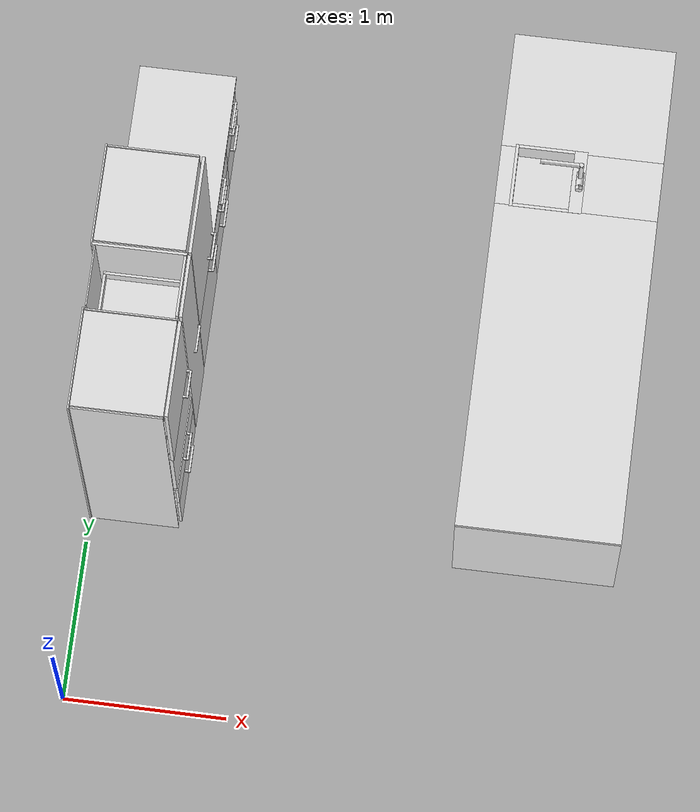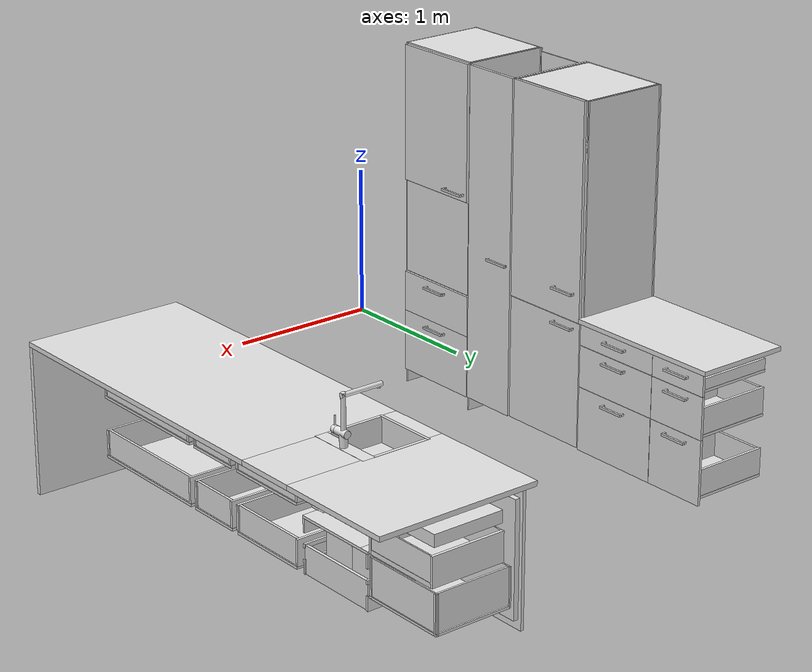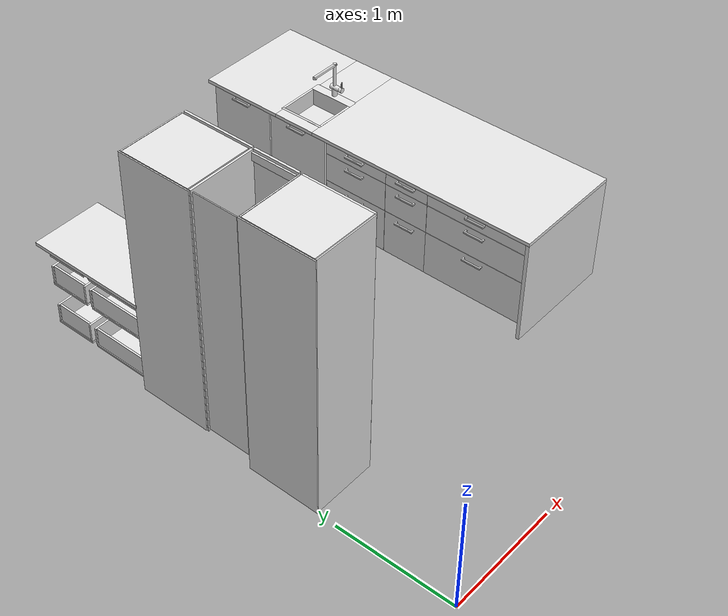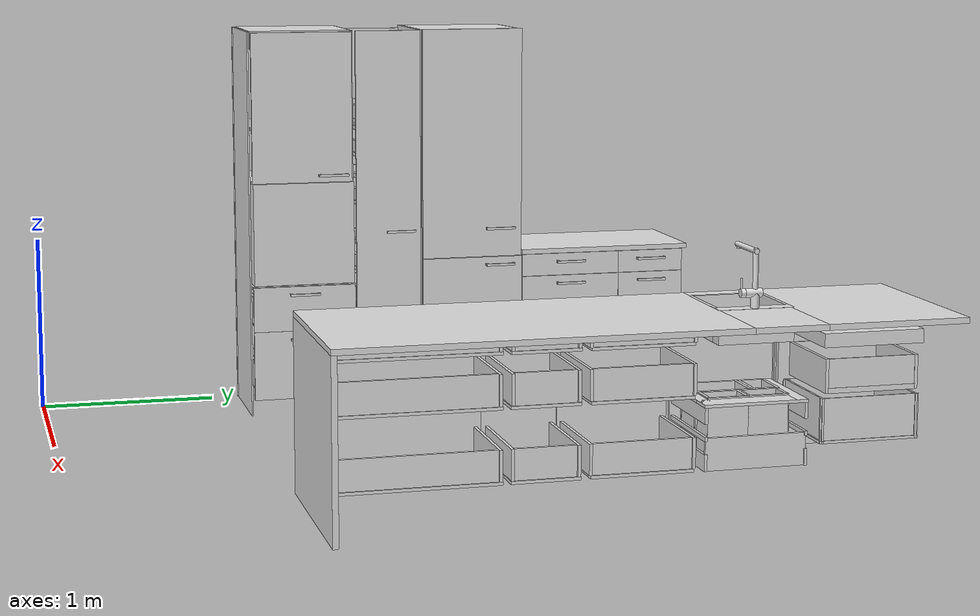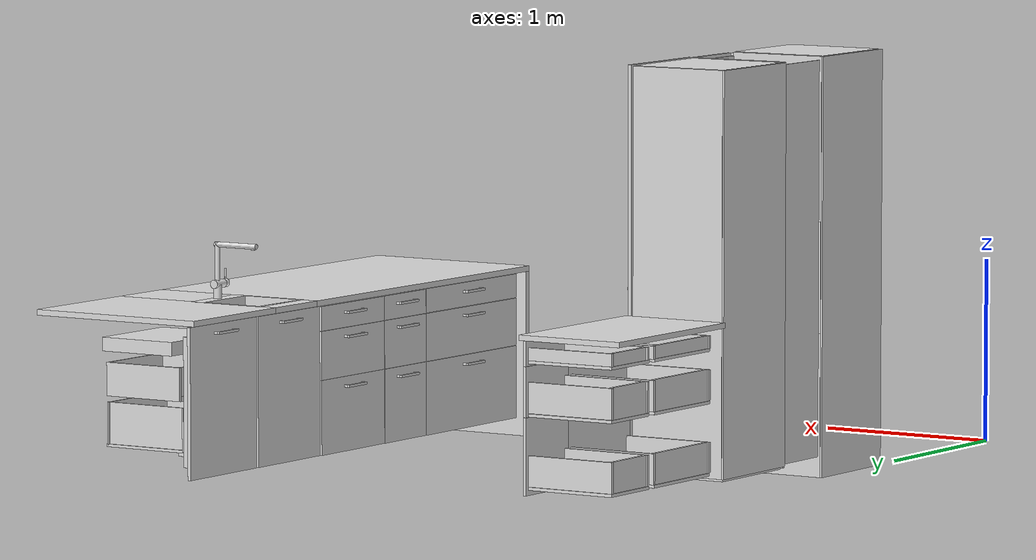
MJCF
<mujoco model="apartment">
	<default>
		<default class="apartment_collision">
			<geom rgba="0.9 0.9 0.9 1.0"/>
		</default>
	</default>
	<asset/>
	<worldbody>
		<body gravcomp="1" name="apartment_root" pos="0.0 0.0 0.0" quat="1.0 0.0 0.0 0.0">
			<inertial mass="9.999999974752427e-07" pos="0.0 0.0 0.0" quat="1.0 0.0 0.0 0.0" diaginertia="9.999999974752427e-07 9.999999974752427e-07 9.999999974752427e-07"/>
			<body gravcomp="1" name="kitchen_root" pos="0.0 0.0 0.0" quat="1.0 0.0 0.0 0.0">
				<inertial mass="9.999999974752427e-07" pos="0.0 0.0 0.0" quat="1.0 0.0 0.0 0.0" diaginertia="9.999999974752427e-07 9.999999974752427e-07 9.999999974752427e-07"/>
				<body gravcomp="1" name="kitchen1_root" pos="0.0 0.0 0.0" quat="1.0 0.0 0.0 0.0">
					<inertial mass="9.999999974752427e-07" pos="0.0 0.0 0.0" quat="1.0 0.0 0.0 0.0" diaginertia="9.999999974752427e-07 9.999999974752427e-07 9.999999974752427e-07"/>
					<body gravcomp="1" name="cabinet6" pos="0.2747659981250763 3.5838398933410645 0.4942069947719574" quat="0.0 0.0 0.0 1.0">
						<inertial mass="275.72900390625" pos="0.04503709822893143 0.000277176994131878 -0.05942520126700401" quat="0.7037742137908936 0.046761613339185715 0.046058811247348785 0.7073851823806763" diaginertia="18.694700241088867 17.97369956970215 9.985130310058594"/>
						<body gravcomp="1" name="cabinet6_drawer1" pos="-0.05329599976539612 -0.0003264900005888194 0.33177798986434937" quat="1.0 0.0 0.0 0.0">
							<inertial mass="39.076698303222656" pos="0.003457420039921999 -4.816129717255535e-07 -0.021292200312018394" quat="2.306210717506474e-06 0.7177302837371826 -2.237420858364203e-06 0.6963212490081787" diaginertia="1.4283499717712402 0.9806399941444397 0.4977079927921295"/>
							<geom name="Geom_199" type="box" pos="-0.23399999737739563 0.0 0.0" quat="1.0 0.0 0.0 0.0" size="0.00800000037997961 0.20000000298023224 0.06499999761581421" class="apartment_collision"/>
							<geom name="Geom_200" type="box" pos="0.02500000037252903 0.0 -0.04500000178813934" quat="1.0 0.0 0.0 0.0" size="0.25 0.18000000715255737 0.00800000037997961" class="apartment_collision"/>
							<geom name="Geom_201" type="box" pos="0.02500000037252903 -0.17000000178813934 -0.004999999888241291" quat="1.0 0.0 0.0 0.0" size="0.25 0.00800000037997961 0.03400000184774399" class="apartment_collision"/>
							<geom name="Geom_202" type="box" pos="0.02500000037252903 0.17000000178813934 -0.004999999888241291" quat="1.0 0.0 0.0 0.0" size="0.25 0.00800000037997961 0.03400000184774399" class="apartment_collision"/>
							<geom name="Geom_203" type="box" pos="0.25999999046325684 0.0 -0.004999999888241291" quat="1.0 0.0 0.0 0.0" size="0.00800000037997961 0.1599999964237213 0.03400000184774399" class="apartment_collision"/>
							<joint name="cabinet6_drawer1_joint" type="slide" pos="0.0 0.0 0.0" armature="0.0" frictionloss="0.0" damping="1000.0" range="0.0 0.44999998807907104" limited="true" stiffness="100"  actuatorfrcrange="0.0 0.0" actuatorfrclimited="false" axis="-1.0 0.0 0.0"/>
							<body gravcomp="1" name="cabinet6_drawer1_handle" pos="-0.26662299036979675 -0.001245990046299994 0.01720389910042286" quat="0.7071067690849304 0.7071067690849304 0.0 0.0">
								<inertial mass="0.10141800343990326" pos="0.00608123978599906 7.626909791724756e-06 0.00021945299522485584" quat="0.7075346112251282 -0.0001653999206610024 -4.868747419095598e-05 0.7066786289215088" diaginertia="0.0003343459975440055 0.000326532986946404 1.0330300028726924e-05"/>
								<geom name="Geom_205" type="box" pos="0.016498500481247902 0.0 0.07999999821186066" quat="1.0 0.0 0.0 0.0" size="0.009999999776482582 0.006500000134110451 0.006500000134110451" class="apartment_collision"/>
								<geom name="Geom_206" type="box" pos="0.0 0.0 0.0" quat="1.0 0.0 0.0 0.0" size="0.006500000134110451 0.006500000134110451 0.08651600033044815" class="apartment_collision"/>
								<geom name="Geom_207" type="box" pos="0.016498500481247902 0.0 -0.07999999821186066" quat="1.0 0.0 0.0 0.0" size="0.009999999776482582 0.006500000134110451 0.006500000134110451" class="apartment_collision"/>
							</body>
						</body>
						<body gravcomp="1" name="cabinet6_drawer2" pos="-0.05305689945816994 -0.0007439699838869274 0.13449999690055847" quat="1.0 0.0 0.0 0.0">
							<inertial mass="64.85150146484375" pos="-0.0035972699988633394 -7.255060268107627e-07 -0.04937160015106201" quat="3.3526416700624395e-06 0.7401803731918335 -2.152341096461896e-07 0.6724083423614502" diaginertia="2.438810110092163 1.9148900508880615 0.915224015712738"/>
							<geom name="Geom_209" type="box" pos="-0.23399999737739563 0.0 0.0" quat="1.0 0.0 0.0 0.0" size="0.00800000037997961 0.20000000298023224 0.12999999523162842" class="apartment_collision"/>
							<geom name="Geom_210" type="box" pos="0.02500000037252903 0.0 -0.11999999731779099" quat="1.0 0.0 0.0 0.0" size="0.25 0.18000000715255737 0.00800000037997961" class="apartment_collision"/>
							<geom name="Geom_211" type="box" pos="0.02500000037252903 -0.17000000178813934 -0.029999999329447746" quat="1.0 0.0 0.0 0.0" size="0.25 0.00800000037997961 0.07999999821186066" class="apartment_collision"/>
							<geom name="Geom_212" type="box" pos="0.02500000037252903 0.17000000178813934 -0.029999999329447746" quat="1.0 0.0 0.0 0.0" size="0.25 0.00800000037997961 0.07999999821186066" class="apartment_collision"/>
							<geom name="Geom_213" type="box" pos="0.25999999046325684 0.0 -0.029999999329447746" quat="1.0 0.0 0.0 0.0" size="0.00800000037997961 0.1599999964237213 0.0820000022649765" class="apartment_collision"/>
							<joint name="cabinet6_drawer2_joint" type="slide" pos="0.0 0.0 0.0" armature="0.0" frictionloss="0.0" damping="1000.0" range="0.0 0.44999998807907104" limited="true" stiffness="100"  actuatorfrcrange="0.0 0.0" actuatorfrclimited="false" axis="-1.0 0.0 0.0"/>
							<body gravcomp="1" name="cabinet6_drawer2_handle" pos="-0.26686200499534607 -0.003978540189564228 0.08541789650917053" quat="0.7071067690849304 0.7071067690849304 0.0 0.0">
								<inertial mass="0.10141800343990326" pos="0.00608123978599906 7.626909791724756e-06 0.00021945299522485584" quat="0.7075346112251282 -0.0001653999206610024 -4.868747419095598e-05 0.7066786289215088" diaginertia="0.0003343459975440055 0.000326532986946404 1.0330300028726924e-05"/>
								<geom name="Geom_215" type="box" pos="0.016498500481247902 0.0 0.07999999821186066" quat="1.0 0.0 0.0 0.0" size="0.009999999776482582 0.006500000134110451 0.006500000134110451" class="apartment_collision"/>
								<geom name="Geom_216" type="box" pos="0.0 0.0 0.0" quat="1.0 0.0 0.0 0.0" size="0.006500000134110451 0.006500000134110451 0.08651600033044815" class="apartment_collision"/>
								<geom name="Geom_217" type="box" pos="0.016498500481247902 0.0 -0.07999999821186066" quat="1.0 0.0 0.0 0.0" size="0.009999999776482582 0.006500000134110451 0.006500000134110451" class="apartment_collision"/>
							</body>
						</body>
						<body gravcomp="1" name="cabinet6_drawer3" pos="-0.052797600626945496 -0.0006945300265215337 -0.19709999859333038" quat="1.0 0.0 0.0 0.0">
							<inertial mass="76.12550354003906" pos="-0.02407040074467659 -8.075890036707278e-07 -0.07856100052595139" quat="5.041550139139872e-06 0.7867890000343323 3.340450120958849e-06 0.617222011089325" diaginertia="2.9339399337768555 2.5349299907684326 1.23062002658844"/>
							<geom name="Geom_189" type="box" pos="-0.23399999737739563 0.0 0.0" quat="1.0 0.0 0.0 0.0" size="0.00800000037997961 0.20000000298023224 0.20000000298023224" class="apartment_collision"/>
							<geom name="Geom_190" type="box" pos="0.02500000037252903 0.0 -0.164000004529953" quat="1.0 0.0 0.0 0.0" size="0.25 0.18000000715255737 0.00800000037997961" class="apartment_collision"/>
							<geom name="Geom_191" type="box" pos="0.02500000037252903 -0.17000000178813934 -0.07500000298023224" quat="1.0 0.0 0.0 0.0" size="0.25 0.00800000037997961 0.07999999821186066" class="apartment_collision"/>
							<geom name="Geom_192" type="box" pos="0.02500000037252903 0.17000000178813934 -0.07500000298023224" quat="1.0 0.0 0.0 0.0" size="0.25 0.00800000037997961 0.07999999821186066" class="apartment_collision"/>
							<geom name="Geom_193" type="box" pos="0.25999999046325684 0.0 -0.07500000298023224" quat="1.0 0.0 0.0 0.0" size="0.00800000037997961 0.1599999964237213 0.07999999821186066" class="apartment_collision"/>
							<joint name="cabinet6_drawer3_joint" type="slide" pos="0.0 0.0 0.0" armature="0.0" frictionloss="0.0" damping="1000.0" range="0.0 0.44999998807907104" limited="true" stiffness="100"  actuatorfrcrange="0.0 0.0" actuatorfrclimited="false" axis="-1.0 0.0 0.0"/>
							<body gravcomp="1" name="cabinet6_drawer3_handle" pos="-0.2671220004558563 -0.004027769900858402 0.15116600692272186" quat="0.7071067690849304 0.7071067690849304 0.0 0.0">
								<inertial mass="0.10141800343990326" pos="0.00608123978599906 7.626909791724756e-06 0.00021945299522485584" quat="0.7075346112251282 -0.0001653999206610024 -4.868747419095598e-05 0.7066786289215088" diaginertia="0.0003343459975440055 0.000326532986946404 1.0330300028726924e-05"/>
								<geom name="Geom_195" type="box" pos="0.016498500481247902 0.0 0.07999999821186066" quat="1.0 0.0 0.0 0.0" size="0.009999999776482582 0.006500000134110451 0.006500000134110451" class="apartment_collision"/>
								<geom name="Geom_196" type="box" pos="0.0 0.0 0.0" quat="1.0 0.0 0.0 0.0" size="0.006500000134110451 0.006500000134110451 0.08651600033044815" class="apartment_collision"/>
								<geom name="Geom_197" type="box" pos="0.016498500481247902 0.0 -0.07999999821186066" quat="1.0 0.0 0.0 0.0" size="0.009999999776482582 0.006500000134110451 0.006500000134110451" class="apartment_collision"/>
							</body>
						</body>
					</body>
					<body gravcomp="1" name="island_cover4" pos="0.2725920081138611 3.7951600551605225 0.44601699709892273" quat="0.0 0.0 0.0 1.0">
						<inertial mass="20.812299728393555" pos="6.627259949709696e-07 -4.21450010890112e-07 8.306139989144867e-07" quat="0.7071067690849304 -9.57797738010413e-07 -9.57797738010413e-07 0.7071067690849304" diaginertia="2.0068199634552 1.3975399732589722 0.6106039881706238"/>
					</body>
					<body gravcomp="1" name="cabinet1" pos="0.28463199734687805 1.4667600393295288 1.1144100427627563" quat="0.0 0.0 0.0 1.0">
						<inertial mass="1469.75" pos="0.021306300535798073 0.029502499848604202 0.22532999515533447" quat="0.9996263384819031 0.011361303739249706 -0.004927041474729776 0.024368908256292343" diaginertia="539.958984375 511.156005859375 82.85890197753906"/>
						<geom name="Geom_221" type="box" pos="0.004999999888241291 0.0 1.065999984741211" quat="1.0 0.0 0.0 0.0" size="0.27000001072883606 0.28999999165534973 0.0494999997317791" class="apartment_collision"/>
						<geom name="Geom_222" type="box" pos="0.2840000092983246 0.0 0.0" quat="1.0 0.0 0.0 0.0" size="0.0044999998062849045 0.3089999854564667 1.1130000352859497" class="apartment_collision"/>
						<geom name="Geom_223" type="box" pos="0.004999999888241291 0.0 -0.36000001430511475" quat="1.0 0.0 0.0 0.0" size="0.27000001072883606 0.28999999165534973 0.007499999832361937" class="apartment_collision"/>
						<geom name="Geom_224" type="box" pos="0.004999999888241291 -0.30000001192092896 0.0" quat="1.0 0.0 0.0 0.0" size="0.27000001072883606 0.0044999998062849045 1.1130000352859497" class="apartment_collision"/>
						<geom name="Geom_225" type="box" pos="0.004999999888241291 0.30000001192092896 0.0" quat="1.0 0.0 0.0 0.0" size="0.27000001072883606 0.0044999998062849045 1.1130000352859497" class="apartment_collision"/>
						<body gravcomp="1" name="cabinet1_drawer1" pos="-0.04679020121693611 -0.011220100335776806 -0.48649999499320984" quat="1.0 0.0 0.0 0.0">
							<inertial mass="95.25170135498047" pos="-0.0019417899893596768 -0.006323240231722593 -0.05017499998211861" quat="0.04405900463461876 0.7392580509185791 -0.039473503828048706 0.6708190441131592" diaginertia="5.06797981262207 2.8646700382232666 2.7893500328063965"/>
							<geom name="Geom_233" type="box" pos="-0.23399999737739563 0.0 0.0" quat="1.0 0.0 0.0 0.0" size="0.00800000037997961 0.2980000078678131 0.12999999523162842" class="apartment_collision"/>
							<geom name="Geom_234" type="box" pos="0.02500000037252903 0.0 -0.11999999731779099" quat="1.0 0.0 0.0 0.0" size="0.25 0.27000001072883606 0.00800000037997961" class="apartment_collision"/>
							<geom name="Geom_235" type="box" pos="0.02500000037252903 -0.27000001072883606 -0.029999999329447746" quat="1.0 0.0 0.0 0.0" size="0.25 0.00800000037997961 0.07999999821186066" class="apartment_collision"/>
							<geom name="Geom_236" type="box" pos="0.02500000037252903 0.27000001072883606 -0.029999999329447746" quat="1.0 0.0 0.0 0.0" size="0.25 0.00800000037997961 0.07999999821186066" class="apartment_collision"/>
							<geom name="Geom_237" type="box" pos="0.25999999046325684 0.0 -0.029999999329447746" quat="1.0 0.0 0.0 0.0" size="0.00800000037997961 0.25999999046325684 0.0820000022649765" class="apartment_collision"/>
							<joint name="cabinet1_drawer1_joint" type="slide" pos="0.0 0.0 0.0" armature="0.0" frictionloss="0.0" damping="1000.0" range="0.0 0.44999998807907104" limited="true" stiffness="100"  actuatorfrcrange="0.0 0.0" actuatorfrclimited="false" axis="-1.0 0.0 0.0"/>
							<body gravcomp="1" name="cabinet1_drawer1_handle" pos="-0.2683179974555969 0.0009181600180454552 0.08401429653167725" quat="0.7071067690849304 0.7071067690849304 0.0 0.0">
								<inertial mass="0.10141800343990326" pos="0.00608123978599906 7.626909791724756e-06 0.00021945299522485584" quat="0.7075346112251282 -0.0001653999206610024 -4.868747419095598e-05 0.7066786289215088" diaginertia="0.0003343459975440055 0.000326532986946404 1.0330300028726924e-05"/>
								<geom name="Geom_239" type="box" pos="0.016498500481247902 0.0 0.07999999821186066" quat="1.0 0.0 0.0 0.0" size="0.009999999776482582 0.006500000134110451 0.006500000134110451" class="apartment_collision"/>
								<geom name="Geom_240" type="box" pos="0.0 0.0 0.0" quat="1.0 0.0 0.0 0.0" size="0.006500000134110451 0.006500000134110451 0.08651600033044815" class="apartment_collision"/>
								<geom name="Geom_241" type="box" pos="0.016498500481247902 0.0 -0.07999999821186066" quat="1.0 0.0 0.0 0.0" size="0.009999999776482582 0.006500000134110451 0.006500000134110451" class="apartment_collision"/>
							</body>
						</body>
						<body gravcomp="1" name="cabinet1_drawer2" pos="-0.04600000008940697 -0.010999999940395355 -0.8169999718666077" quat="1.0 0.0 0.0 0.0">
							<inertial mass="114.78700256347656" pos="-0.021780800074338913 -6.294259833339311e-07 -0.07886719703674316" quat="1.0027593816630542e-05 0.7857874631881714 -6.472895620390773e-06 0.6184965968132019" diaginertia="6.151130199432373 3.816970109939575 3.5750598907470703"/>
							<geom name="Geom_243" type="box" pos="-0.23399999737739563 0.0 0.0" quat="1.0 0.0 0.0 0.0" size="0.00800000037997961 0.2980000078678131 0.20000000298023224" class="apartment_collision"/>
							<geom name="Geom_244" type="box" pos="0.02500000037252903 0.0 -0.164000004529953" quat="1.0 0.0 0.0 0.0" size="0.25 0.27000001072883606 0.00800000037997961" class="apartment_collision"/>
							<geom name="Geom_245" type="box" pos="0.02500000037252903 -0.27000001072883606 -0.07500000298023224" quat="1.0 0.0 0.0 0.0" size="0.25 0.00800000037997961 0.07999999821186066" class="apartment_collision"/>
							<geom name="Geom_246" type="box" pos="0.02500000037252903 0.27000001072883606 -0.07500000298023224" quat="1.0 0.0 0.0 0.0" size="0.25 0.00800000037997961 0.07999999821186066" class="apartment_collision"/>
							<geom name="Geom_247" type="box" pos="0.25999999046325684 0.0 -0.07500000298023224" quat="1.0 0.0 0.0 0.0" size="0.00800000037997961 0.25999999046325684 0.07999999821186066" class="apartment_collision"/>
							<joint name="cabinet1_drawer2_joint" type="slide" pos="0.0 0.0 0.0" armature="0.0" frictionloss="0.0" damping="1000.0" range="0.0 0.44999998807907104" limited="true" stiffness="100"  actuatorfrcrange="0.0 0.0" actuatorfrclimited="false" axis="-1.0 0.0 0.0"/>
							<body gravcomp="1" name="cabinet1_drawer2_handle" pos="-0.2694830000400543 -0.001458449987694621 0.15060600638389587" quat="0.7071067690849304 0.7071067690849304 0.0 0.0">
								<inertial mass="0.10141800343990326" pos="0.00608123978599906 7.626909791724756e-06 0.00021945299522485584" quat="0.7075346112251282 -0.0001653999206610024 -4.868747419095598e-05 0.7066786289215088" diaginertia="0.0003343459975440055 0.000326532986946404 1.0330300028726924e-05"/>
								<geom name="Geom_249" type="box" pos="0.016498500481247902 0.0 0.07999999821186066" quat="1.0 0.0 0.0 0.0" size="0.009999999776482582 0.006500000134110451 0.006500000134110451" class="apartment_collision"/>
								<geom name="Geom_250" type="box" pos="0.0 0.0 0.0" quat="1.0 0.0 0.0 0.0" size="0.006500000134110451 0.006500000134110451 0.08651600033044815" class="apartment_collision"/>
								<geom name="Geom_251" type="box" pos="0.016498500481247902 0.0 -0.07999999821186066" quat="1.0 0.0 0.0 0.0" size="0.009999999776482582 0.006500000134110451 0.006500000134110451" class="apartment_collision"/>
							</body>
						</body>
						<body gravcomp="1" name="cabinet1_shelf1" pos="0.009901000186800957 0.0005000000237487257 0.5600000023841858" quat="1.0 0.0 0.0 0.0">
							<inertial mass="9.0181303024292" pos="0.0 0.0 0.0" quat="0.0 0.7071067690849304 0.0 0.7071067690849304" diaginertia="0.4523620009422302 0.23747700452804565 0.2152239978313446"/>
							<geom name="Geom_253" type="box" pos="0.004999999888241291 0.0 0.0" quat="1.0 0.0 0.0 0.0" size="0.27000001072883606 0.28999999165534973 0.007499999832361937" class="apartment_collision"/>
						</body>
						<body gravcomp="1" name="oven" pos="-0.2739590108394623 -0.012359700165688992 -0.3426719903945923" quat="1.0 0.0 0.0 0.0">
							<inertial mass="509.9020080566406" pos="0.27100300788879395 0.0214719008654356 0.31152600049972534" quat="0.9472455978393555 0.0725022703409195 -0.3085738718509674 0.04744808003306389" diaginertia="31.142200469970703 26.6737003326416 25.97209930419922"/>
							<geom name="Geom_257" type="box" pos="0.27000001072883606 0.0 0.28999999165534973" quat="1.0 0.0 0.0 0.0" size="0.27900001406669617 0.2930000126361847 0.29499998688697815" class="apartment_collision"/>
							<body gravcomp="1" name="oven_door" pos="0.0 0.0 0.0" quat="0.5 0.5 0.5 -0.5">
								<inertial mass="30.66830062866211" pos="-0.22755999863147736 0.004878609906882048 -0.002999390009790659" quat="0.7074032425880432 -1.1907503903785255e-05 -1.1897504009539261e-05 0.7068102359771729" diaginertia="1.3503400087356567 0.8070060014724731 0.5493580102920532"/>
							</body>
						</body>
						<body gravcomp="1" name="cabinet1_shelf2" pos="0.009901000186800957 0.0005000000237487257 0.24950100481510162" quat="1.0 0.0 0.0 0.0">
							<inertial mass="9.0181303024292" pos="0.0 0.0 0.0" quat="0.5 0.5 -0.5 0.5" diaginertia="0.4523620009422302 0.22634999454021454 0.22634999454021454"/>
							<geom name="Geom_255" type="box" pos="0.004999999888241291 0.0 0.0" quat="1.0 0.0 0.0 0.0" size="0.27000001072883606 0.28999999165534973 0.007499999832361937" class="apartment_collision"/>
						</body>
						<body gravcomp="1" name="cabinet1_door" pos="-0.2800000011920929 0.2800000011920929 0.6769999861717224" quat="1.0 0.0 0.0 0.0">
							<inertial mass="20.15690040588379" pos="-0.00020631200459320098 -0.28013598918914795 9.700589725980535e-05" quat="0.9999992847442627 -0.0011547303292900324 2.9820506597388885e-07 -0.0003923721087630838" diaginertia="1.872499942779541 1.2673100233078003 0.6064220070838928"/>
							<geom name="Geom_227" type="box" pos="0.0 -0.2849999964237213 0.0" quat="1.0 0.0 0.0 0.0" size="0.009999999776482582 0.28999999165534973 0.4300000071525574" class="apartment_collision"/>
							<joint name="cabinet1_door_joint" type="hinge" pos="0.0 0.0 0.0" armature="0.0" frictionloss="0.0" damping="1000.0" range="0.0 1.5707999467849731" limited="true" stiffness="100"  actuatorfrcrange="0.0 0.0" actuatorfrclimited="false" axis="0.0 0.0 -1.0"/>
							<body gravcomp="1" name="cabinet1_door_handle" pos="-0.03598880022764206 -0.4631560146808624 -0.3898339867591858" quat="0.7071067690849304 0.7071067690849304 0.0 0.0">
								<inertial mass="0.10141800343990326" pos="0.00608123978599906 7.626909791724756e-06 0.00021945299522485584" quat="0.7075346112251282 -0.0001653999206610024 -4.868747419095598e-05 0.7066786289215088" diaginertia="0.0003343459975440055 0.000326532986946404 1.0330300028726924e-05"/>
								<geom name="Geom_229" type="box" pos="0.016498500481247902 0.0 0.07999999821186066" quat="1.0 0.0 0.0 0.0" size="0.009999999776482582 0.006500000134110451 0.006500000134110451" class="apartment_collision"/>
								<geom name="Geom_230" type="box" pos="0.0 0.0 0.0" quat="1.0 0.0 0.0 0.0" size="0.006500000134110451 0.006500000134110451 0.08651600033044815" class="apartment_collision"/>
								<geom name="Geom_231" type="box" pos="0.016498500481247902 0.0 -0.07999999821186066" quat="1.0 0.0 0.0 0.0" size="0.009999999776482582 0.006500000134110451 0.006500000134110451" class="apartment_collision"/>
							</body>
						</body>
					</body>
					<body gravcomp="1" name="counter_wall" pos="0.2814280092716217 3.2949399948120117 0.9089210033416748" quat="0.0 0.0 0.0 1.0">
						<inertial mass="34.350799560546875" pos="0.0 -0.000610848015639931 -0.00021701199875678867" quat="0.5 0.5 -0.5 0.5" diaginertia="4.067590236663818 3.0411200523376465 1.0309200286865234"/>
						<geom name="Geom_260" type="box" pos="0.0 0.0 0.0" quat="1.0 0.0 0.0 0.0" size="0.30000001192092896 0.5139999985694885 0.014000000432133675" class="apartment_collision"/>
					</body>
					<body gravcomp="1" name="cabinet5" pos="0.2747659981250763 3.084120035171509 0.4942069947719574" quat="0.0 0.0 0.0 1.0">
						<inertial mass="400.802001953125" pos="0.049657199531793594 2.2528000044985674e-05 -0.06275369971990585" quat="0.9974408745765686 0.0003722599649336189 0.07149479538202286 -4.00551944039762e-05" diaginertia="34.55110168457031 26.862300872802734 22.98740005493164"/>
						<body gravcomp="1" name="cabinet5_drawer1" pos="-0.05262700095772743 -0.0010002600029110909 0.33177798986434937" quat="1.0 0.0 0.0 0.0">
							<inertial mass="57.67430114746094" pos="0.0011586700566112995 -2.902810081195639e-07 -0.021432699635624886" quat="0.5071611404418945 0.5071701407432556 -0.4927261471748352 0.4927341639995575" diaginertia="3.094759941101074 1.716480016708374 1.4527000188827515"/>
							<geom name="Geom_347" type="box" pos="-0.23399999737739563 0.0 0.0" quat="1.0 0.0 0.0 0.0" size="0.00800000037997961 0.2980000078678131 0.06499999761581421" class="apartment_collision"/>
							<geom name="Geom_348" type="box" pos="0.02500000037252903 0.0 -0.04500000178813934" quat="1.0 0.0 0.0 0.0" size="0.25 0.27000001072883606 0.00800000037997961" class="apartment_collision"/>
							<geom name="Geom_349" type="box" pos="0.02500000037252903 -0.27000001072883606 -0.004999999888241291" quat="1.0 0.0 0.0 0.0" size="0.25 0.00800000037997961 0.03400000184774399" class="apartment_collision"/>
							<geom name="Geom_350" type="box" pos="0.02500000037252903 0.27000001072883606 -0.004999999888241291" quat="1.0 0.0 0.0 0.0" size="0.25 0.00800000037997961 0.03400000184774399" class="apartment_collision"/>
							<geom name="Geom_351" type="box" pos="0.25999999046325684 0.0 -0.004999999888241291" quat="1.0 0.0 0.0 0.0" size="0.00800000037997961 0.25999999046325684 0.03400000184774399" class="apartment_collision"/>
							<joint name="cabinet5_drawer1_joint" type="slide" pos="0.0 0.0 0.0" armature="0.0" frictionloss="0.0" damping="1000.0" range="0.0 0.44999998807907104" limited="true" stiffness="100"  actuatorfrcrange="0.0 0.0" actuatorfrclimited="false" axis="-1.0 0.0 0.0"/>
							<body gravcomp="1" name="cabinet5_drawer1_handle" pos="-0.2698090076446533 0.001423630048520863 0.016769500449299812" quat="0.7071067690849304 0.7071067690849304 0.0 0.0">
								<inertial mass="0.10141800343990326" pos="0.00608123978599906 7.626909791724756e-06 0.00021945299522485584" quat="0.7075346112251282 -0.0001653999206610024 -4.868747419095598e-05 0.7066786289215088" diaginertia="0.0003343459975440055 0.000326532986946404 1.0330300028726924e-05"/>
								<geom name="Geom_353" type="box" pos="0.016498500481247902 0.0 0.07999999821186066" quat="1.0 0.0 0.0 0.0" size="0.009999999776482582 0.006500000134110451 0.006500000134110451" class="apartment_collision"/>
								<geom name="Geom_354" type="box" pos="0.0 0.0 0.0" quat="1.0 0.0 0.0 0.0" size="0.006500000134110451 0.006500000134110451 0.08651600033044815" class="apartment_collision"/>
								<geom name="Geom_355" type="box" pos="0.016498500481247902 0.0 -0.07999999821186066" quat="1.0 0.0 0.0 0.0" size="0.009999999776482582 0.006500000134110451 0.006500000134110451" class="apartment_collision"/>
							</body>
						</body>
						<body gravcomp="1" name="cabinet5_drawer2" pos="-0.053037598729133606 -0.0007915199967101216 0.13449999690055847" quat="1.0 0.0 0.0 0.0">
							<inertial mass="98.095703125" pos="-0.001801009988412261 -6.371479912559153e-07 -0.05033480003476143" quat="0.5234497785568237 0.5235407948493958 -0.4753037989139557 0.4753858149051666" diaginertia="5.241300106048584 2.9346001148223877 2.8931798934936523"/>
							<geom name="Geom_357" type="box" pos="-0.23399999737739563 0.0 0.0" quat="1.0 0.0 0.0 0.0" size="0.00800000037997961 0.2980000078678131 0.12999999523162842" class="apartment_collision"/>
							<geom name="Geom_358" type="box" pos="0.02500000037252903 0.0 -0.11999999731779099" quat="1.0 0.0 0.0 0.0" size="0.25 0.27000001072883606 0.00800000037997961" class="apartment_collision"/>
							<geom name="Geom_359" type="box" pos="0.02500000037252903 -0.27000001072883606 -0.029999999329447746" quat="1.0 0.0 0.0 0.0" size="0.25 0.00800000037997961 0.07999999821186066" class="apartment_collision"/>
							<geom name="Geom_360" type="box" pos="0.02500000037252903 0.27000001072883606 -0.029999999329447746" quat="1.0 0.0 0.0 0.0" size="0.25 0.00800000037997961 0.07999999821186066" class="apartment_collision"/>
							<geom name="Geom_361" type="box" pos="0.25999999046325684 0.0 -0.029999999329447746" quat="1.0 0.0 0.0 0.0" size="0.00800000037997961 0.25999999046325684 0.0820000022649765" class="apartment_collision"/>
							<joint name="cabinet5_drawer2_joint" type="slide" pos="0.0 0.0 0.0" armature="0.0" frictionloss="0.0" damping="1000.0" range="0.0 0.44999998807907104" limited="true" stiffness="100"  actuatorfrcrange="0.0 0.0" actuatorfrclimited="false" axis="-1.0 0.0 0.0"/>
							<body gravcomp="1" name="cabinet5_drawer2_handle" pos="-0.2707110047340393 0.0010641299886628985 0.0850083976984024" quat="0.7071067690849304 0.7071067690849304 0.0 0.0">
								<inertial mass="0.10141800343990326" pos="0.00608123978599906 7.626909791724756e-06 0.00021945299522485584" quat="0.7075346112251282 -0.0001653999206610024 -4.868747419095598e-05 0.7066786289215088" diaginertia="0.0003343459975440055 0.000326532986946404 1.0330300028726924e-05"/>
								<geom name="Geom_363" type="box" pos="0.016498500481247902 0.0 0.07999999821186066" quat="1.0 0.0 0.0 0.0" size="0.009999999776482582 0.006500000134110451 0.006500000134110451" class="apartment_collision"/>
								<geom name="Geom_364" type="box" pos="0.0 0.0 0.0" quat="1.0 0.0 0.0 0.0" size="0.006500000134110451 0.006500000134110451 0.08651600033044815" class="apartment_collision"/>
								<geom name="Geom_365" type="box" pos="0.016498500481247902 0.0 -0.07999999821186066" quat="1.0 0.0 0.0 0.0" size="0.009999999776482582 0.006500000134110451 0.006500000134110451" class="apartment_collision"/>
							</body>
						</body>
						<body gravcomp="1" name="cabinet5_drawer3" pos="-0.05345090106129646 -0.0007555100019089878 -0.19709999859333038" quat="1.0 0.0 0.0 0.0">
							<inertial mass="115.125" pos="-0.02201079949736595 -6.431000088014116e-07 -0.07959750294685364" quat="1.1111600542790256e-05 0.7870470285415649 -7.225330136861885e-06 0.6168929934501648" diaginertia="6.18025016784668 3.834820032119751 3.599299907684326"/>
							<geom name="Geom_337" type="box" pos="-0.23399999737739563 0.0 0.0" quat="1.0 0.0 0.0 0.0" size="0.00800000037997961 0.2980000078678131 0.20000000298023224" class="apartment_collision"/>
							<geom name="Geom_338" type="box" pos="0.02500000037252903 0.0 -0.164000004529953" quat="1.0 0.0 0.0 0.0" size="0.25 0.27000001072883606 0.00800000037997961" class="apartment_collision"/>
							<geom name="Geom_339" type="box" pos="0.02500000037252903 -0.27000001072883606 -0.07500000298023224" quat="1.0 0.0 0.0 0.0" size="0.25 0.00800000037997961 0.07999999821186066" class="apartment_collision"/>
							<geom name="Geom_340" type="box" pos="0.02500000037252903 0.27000001072883606 -0.07500000298023224" quat="1.0 0.0 0.0 0.0" size="0.25 0.00800000037997961 0.07999999821186066" class="apartment_collision"/>
							<geom name="Geom_341" type="box" pos="0.25999999046325684 0.0 -0.07500000298023224" quat="1.0 0.0 0.0 0.0" size="0.00800000037997961 0.25999999046325684 0.07999999821186066" class="apartment_collision"/>
							<joint name="cabinet5_drawer3_joint" type="slide" pos="0.0 0.0 0.0" armature="0.0" frictionloss="0.0" damping="1000.0" range="0.0 0.44999998807907104" limited="true" stiffness="100"  actuatorfrcrange="0.0 0.0" actuatorfrclimited="false" axis="-1.0 0.0 0.0"/>
							<body gravcomp="1" name="cabinet5_drawer3_handle" pos="-0.26888200640678406 0.0010287499753758311 0.1502700001001358" quat="0.7071067690849304 0.7071067690849304 0.0 0.0">
								<inertial mass="0.10141800343990326" pos="0.00608123978599906 7.626909791724756e-06 0.00021945299522485584" quat="0.7075346112251282 -0.0001653999206610024 -4.868747419095598e-05 0.7066786289215088" diaginertia="0.0003343459975440055 0.000326532986946404 1.0330300028726924e-05"/>
								<geom name="Geom_343" type="box" pos="0.016498500481247902 0.0 0.07999999821186066" quat="1.0 0.0 0.0 0.0" size="0.009999999776482582 0.006500000134110451 0.006500000134110451" class="apartment_collision"/>
								<geom name="Geom_344" type="box" pos="0.0 0.0 0.0" quat="1.0 0.0 0.0 0.0" size="0.006500000134110451 0.006500000134110451 0.08651600033044815" class="apartment_collision"/>
								<geom name="Geom_345" type="box" pos="0.016498500481247902 0.0 -0.07999999821186066" quat="1.0 0.0 0.0 0.0" size="0.009999999776482582 0.006500000134110451 0.006500000134110451" class="apartment_collision"/>
							</body>
						</body>
					</body>
					<body gravcomp="1" name="cabinet2" pos="0.27990901470184326 1.9770499467849731 1.1623899936676025" quat="0.0 0.0 0.0 1.0">
						<inertial mass="870.2239990234375" pos="0.020062899217009544 0.0004990639863535762 0.14528000354766846" quat="0.720766007900238 -0.0027324699331074953 -0.002903080079704523 0.693166971206665" diaginertia="361.9209899902344 359.5270080566406 29.0664005279541"/>
						<geom name="Geom_367" type="box" pos="0.2673720121383667 0.0 0.0" quat="1.0 0.0 0.0 0.0" size="0.004000000189989805 0.1838819980621338 1.0478399991989136" class="apartment_collision"/>
						<geom name="Geom_368" type="box" pos="0.005896999966353178 -0.19197900593280792 0.0" quat="1.0 0.0 0.0 0.0" size="0.2773590087890625 0.00800000037997961 1.0638400316238403" class="apartment_collision"/>
						<geom name="Geom_369" type="box" pos="-0.2603900134563446 0.0 1.0158400535583496" quat="1.0 0.0 0.0 0.0" size="0.007187000010162592 0.1838819980621338 0.031996000558137894" class="apartment_collision"/>
						<body gravcomp="1" name="cabinet2_drawer5" pos="-0.004647749941796064 0.001345379976555705 -0.5180960297584534" quat="1.0 0.0 0.0 0.0">
							<inertial mass="53.40129852294922" pos="0.0061420900747179985 0.00021431100321933627 -0.029991300776600838" quat="-0.0002616059500724077 0.701400876045227 0.00027150995447300375 0.7127668857574463" diaginertia="1.871209979057312 1.3533899784088135 0.7296550273895264"/>
							<geom name="Geom_377" type="box" pos="-0.24286900460720062 0.14842799305915833 0.0" quat="1.0 0.0 0.0 0.0" size="0.00839299988001585 0.03244100138545036 0.09098999947309494" class="apartment_collision"/>
							<geom name="Geom_378" type="box" pos="-0.24286900460720062 -0.14842799305915833 0.0" quat="1.0 0.0 0.0 0.0" size="0.00839299988001585 0.03244100138545036 0.09098999947309494" class="apartment_collision"/>
							<geom name="Geom_379" type="box" pos="-0.003984000068157911 0.0 -0.08024200052022934" quat="1.0 0.0 0.0 0.0" size="0.24748900532722473 0.18098099529743195 0.010749000124633312" class="apartment_collision"/>
							<geom name="Geom_380" type="box" pos="-0.003984000068157911 0.1705780029296875 0.07534199953079224" quat="1.0 0.0 0.0 0.0" size="0.24748900532722473 0.00800000037997961 0.011649000458419323" class="apartment_collision"/>
							<geom name="Geom_381" type="box" pos="-0.003984000068157911 -0.1705780029296875 0.07534199953079224" quat="1.0 0.0 0.0 0.0" size="0.24748900532722473 0.00800000037997961 0.011649000458419323" class="apartment_collision"/>
							<geom name="Geom_382" type="box" pos="-0.003984000068157911 0.1705780029296875 -0.04374299943447113" quat="1.0 0.0 0.0 0.0" size="0.24748900532722473 0.00800000037997961 0.04355299845337868" class="apartment_collision"/>
							<geom name="Geom_383" type="box" pos="-0.003984000068157911 -0.1705780029296875 -0.04374299943447113" quat="1.0 0.0 0.0 0.0" size="0.24748900532722473 0.00800000037997961 0.04355299845337868" class="apartment_collision"/>
							<geom name="Geom_384" type="box" pos="-0.2423740029335022 0.0 0.06084299832582474" quat="1.0 0.0 0.0 0.0" size="0.006897999905049801 0.18098099529743195 0.010149000212550163" class="apartment_collision"/>
							<geom name="Geom_385" type="box" pos="-0.2423740029335022 0.0 -0.041999999433755875" quat="1.0 0.0 0.0 0.0" size="0.006897999905049801 0.18098099529743195 0.04899999871850014" class="apartment_collision"/>
							<geom name="Geom_386" type="box" pos="0.23544099926948547 0.0 0.0" quat="1.0 0.0 0.0 0.0" size="0.008063999935984612 0.18098099529743195 0.09087900072336197" class="apartment_collision"/>
							<joint name="cabinet2_drawer5_joint" type="slide" pos="0.0 0.0 0.0" armature="0.0" frictionloss="0.0" damping="1000.0" range="0.0 0.44999998807907104" limited="true" stiffness="100"  actuatorfrcrange="0.0 0.0" actuatorfrclimited="false" axis="-1.0 0.0 0.0"/>
						</body>
						<body gravcomp="1" name="cabinet2_drawer6" pos="-0.004647749941796064 0.001345379976555705 -0.9551920294761658" quat="1.0 0.0 0.0 0.0">
							<inertial mass="53.40129852294922" pos="0.0061420900747179985 0.00021431100321933627 -0.029991300776600838" quat="-0.0002616059500724077 0.701400876045227 0.00027150995447300375 0.7127668857574463" diaginertia="1.871209979057312 1.3533899784088135 0.7296550273895264"/>
							<geom name="Geom_399" type="box" pos="-0.24286900460720062 0.14842799305915833 0.0" quat="1.0 0.0 0.0 0.0" size="0.00839299988001585 0.03244100138545036 0.09098999947309494" class="apartment_collision"/>
							<geom name="Geom_400" type="box" pos="-0.003984000068157911 -0.1705780029296875 0.07534199953079224" quat="1.0 0.0 0.0 0.0" size="0.24748900532722473 0.00800000037997961 0.011649000458419323" class="apartment_collision"/>
							<geom name="Geom_401" type="box" pos="-0.003984000068157911 0.0 -0.08024200052022934" quat="1.0 0.0 0.0 0.0" size="0.24748900532722473 0.18098099529743195 0.010749000124633312" class="apartment_collision"/>
							<geom name="Geom_402" type="box" pos="0.23544099926948547 0.0 0.0" quat="1.0 0.0 0.0 0.0" size="0.008063999935984612 0.18098099529743195 0.09087900072336197" class="apartment_collision"/>
							<geom name="Geom_403" type="box" pos="-0.2423740029335022 0.0 0.06084299832582474" quat="1.0 0.0 0.0 0.0" size="0.006897999905049801 0.18098099529743195 0.010149000212550163" class="apartment_collision"/>
							<geom name="Geom_404" type="box" pos="-0.2423740029335022 0.0 -0.041999999433755875" quat="1.0 0.0 0.0 0.0" size="0.006897999905049801 0.18098099529743195 0.04899999871850014" class="apartment_collision"/>
							<geom name="Geom_405" type="box" pos="-0.003984000068157911 0.1705780029296875 0.07534199953079224" quat="1.0 0.0 0.0 0.0" size="0.24748900532722473 0.00800000037997961 0.011649000458419323" class="apartment_collision"/>
							<geom name="Geom_406" type="box" pos="-0.24286900460720062 -0.14842799305915833 0.0" quat="1.0 0.0 0.0 0.0" size="0.00839299988001585 0.03244100138545036 0.09098999947309494" class="apartment_collision"/>
							<geom name="Geom_407" type="box" pos="-0.003984000068157911 -0.1705780029296875 -0.04374299943447113" quat="1.0 0.0 0.0 0.0" size="0.24748900532722473 0.00800000037997961 0.04355299845337868" class="apartment_collision"/>
							<geom name="Geom_408" type="box" pos="-0.003984000068157911 0.1705780029296875 -0.04374299943447113" quat="1.0 0.0 0.0 0.0" size="0.24748900532722473 0.00800000037997961 0.04355299845337868" class="apartment_collision"/>
							<joint name="cabinet2_drawer6_joint" type="slide" pos="0.0 0.0 0.0" armature="0.0" frictionloss="0.0" damping="1000.0" range="0.0 0.44999998807907104" limited="true" stiffness="100"  actuatorfrcrange="0.0 0.0" actuatorfrclimited="false" axis="-1.0 0.0 0.0"/>
						</body>
						<body gravcomp="1" name="cabinet2_drawer3" pos="-0.004647749941796064 -0.001345379976555705 0.14289699494838715" quat="1.0 0.0 0.0 0.0">
							<inertial mass="53.40129852294922" pos="0.0061420900747179985 0.00021431100321933627 -0.029991300776600838" quat="-0.0002616059500724077 0.701400876045227 0.00027150995447300375 0.7127668857574463" diaginertia="1.871209979057312 1.3533899784088135 0.7296550273895264"/>
							<geom name="Geom_416" type="box" pos="-0.003984000068157911 -0.1705780029296875 -0.04374299943447113" quat="1.0 0.0 0.0 0.0" size="0.24748900532722473 0.00800000037997961 0.04355299845337868" class="apartment_collision"/>
							<geom name="Geom_417" type="box" pos="-0.2423740029335022 0.0 -0.041999999433755875" quat="1.0 0.0 0.0 0.0" size="0.006897999905049801 0.18098099529743195 0.04899999871850014" class="apartment_collision"/>
							<geom name="Geom_418" type="box" pos="-0.003984000068157911 0.1705780029296875 0.07534199953079224" quat="1.0 0.0 0.0 0.0" size="0.24748900532722473 0.00800000037997961 0.011649000458419323" class="apartment_collision"/>
							<geom name="Geom_419" type="box" pos="0.23544099926948547 0.0 0.0" quat="1.0 0.0 0.0 0.0" size="0.008063999935984612 0.18098099529743195 0.09087900072336197" class="apartment_collision"/>
							<geom name="Geom_420" type="box" pos="-0.2423740029335022 0.0 0.06084299832582474" quat="1.0 0.0 0.0 0.0" size="0.006897999905049801 0.18098099529743195 0.010149000212550163" class="apartment_collision"/>
							<geom name="Geom_421" type="box" pos="-0.003984000068157911 0.1705780029296875 -0.04374299943447113" quat="1.0 0.0 0.0 0.0" size="0.24748900532722473 0.00800000037997961 0.04355299845337868" class="apartment_collision"/>
							<geom name="Geom_422" type="box" pos="-0.003984000068157911 0.0 -0.08024200052022934" quat="1.0 0.0 0.0 0.0" size="0.24748900532722473 0.18098099529743195 0.010749000124633312" class="apartment_collision"/>
							<geom name="Geom_423" type="box" pos="-0.003984000068157911 -0.1705780029296875 0.07534199953079224" quat="1.0 0.0 0.0 0.0" size="0.24748900532722473 0.00800000037997961 0.011649000458419323" class="apartment_collision"/>
							<geom name="Geom_424" type="box" pos="-0.24286900460720062 -0.14842799305915833 0.0" quat="1.0 0.0 0.0 0.0" size="0.00839299988001585 0.03244100138545036 0.09098999947309494" class="apartment_collision"/>
							<geom name="Geom_425" type="box" pos="-0.24286900460720062 0.14842799305915833 0.0" quat="1.0 0.0 0.0 0.0" size="0.00839299988001585 0.03244100138545036 0.09098999947309494" class="apartment_collision"/>
							<joint name="cabinet2_drawer3_joint" type="slide" pos="0.0 0.0 0.0" armature="0.0" frictionloss="0.0" damping="1000.0" range="0.0 0.44999998807907104" limited="true" stiffness="100"  actuatorfrcrange="0.0 0.0" actuatorfrclimited="false" axis="-1.0 0.0 0.0"/>
						</body>
						<body gravcomp="1" name="cabinet2_drawer4" pos="-0.004647749941796064 0.001345379976555705 -0.24243700504302979" quat="1.0 0.0 0.0 0.0">
							<inertial mass="53.40129852294922" pos="0.0061420900747179985 0.00021431100321933627 -0.029991300776600838" quat="-0.0002616059500724077 0.701400876045227 0.00027150995447300375 0.7127668857574463" diaginertia="1.871209979057312 1.3533899784088135 0.7296550273895264"/>
							<geom name="Geom_428" type="box" pos="-0.003984000068157911 0.1705780029296875 0.07534199953079224" quat="1.0 0.0 0.0 0.0" size="0.24748900532722473 0.00800000037997961 0.011649000458419323" class="apartment_collision"/>
							<geom name="Geom_429" type="box" pos="-0.2423740029335022 0.0 -0.041999999433755875" quat="1.0 0.0 0.0 0.0" size="0.006897999905049801 0.18098099529743195 0.04899999871850014" class="apartment_collision"/>
							<geom name="Geom_430" type="box" pos="-0.24286900460720062 -0.14842799305915833 0.0" quat="1.0 0.0 0.0 0.0" size="0.00839299988001585 0.03244100138545036 0.09098999947309494" class="apartment_collision"/>
							<geom name="Geom_431" type="box" pos="-0.2423740029335022 0.0 0.06084299832582474" quat="1.0 0.0 0.0 0.0" size="0.006897999905049801 0.18098099529743195 0.010149000212550163" class="apartment_collision"/>
							<geom name="Geom_432" type="box" pos="0.23544099926948547 0.0 0.0" quat="1.0 0.0 0.0 0.0" size="0.008063999935984612 0.18098099529743195 0.09087900072336197" class="apartment_collision"/>
							<geom name="Geom_433" type="box" pos="-0.003984000068157911 -0.1705780029296875 0.07534199953079224" quat="1.0 0.0 0.0 0.0" size="0.24748900532722473 0.00800000037997961 0.011649000458419323" class="apartment_collision"/>
							<geom name="Geom_434" type="box" pos="-0.24286900460720062 0.14842799305915833 0.0" quat="1.0 0.0 0.0 0.0" size="0.00839299988001585 0.03244100138545036 0.09098999947309494" class="apartment_collision"/>
							<geom name="Geom_435" type="box" pos="-0.003984000068157911 0.0 -0.08024200052022934" quat="1.0 0.0 0.0 0.0" size="0.24748900532722473 0.18098099529743195 0.010749000124633312" class="apartment_collision"/>
							<geom name="Geom_436" type="box" pos="-0.003984000068157911 0.1705780029296875 -0.04374299943447113" quat="1.0 0.0 0.0 0.0" size="0.24748900532722473 0.00800000037997961 0.04355299845337868" class="apartment_collision"/>
							<geom name="Geom_437" type="box" pos="-0.003984000068157911 -0.1705780029296875 -0.04374299943447113" quat="1.0 0.0 0.0 0.0" size="0.24748900532722473 0.00800000037997961 0.04355299845337868" class="apartment_collision"/>
							<joint name="cabinet2_drawer4_joint" type="slide" pos="0.0 0.0 0.0" armature="0.0" frictionloss="0.0" damping="1000.0" range="0.0 0.44999998807907104" limited="true" stiffness="100"  actuatorfrcrange="0.0 0.0" actuatorfrclimited="false" axis="-1.0 0.0 0.0"/>
						</body>
						<body gravcomp="1" name="cabinet2_drawer1" pos="-0.004647749941796064 0.001345379976555705 0.5804619789123535" quat="1.0 0.0 0.0 0.0">
							<inertial mass="36.980499267578125" pos="-0.002493930049240589 0.0002059880062006414 -0.014837300404906273" quat="-0.0002871279721148312 0.7084628939628601 0.000286026974208653 0.7057479023933411" diaginertia="1.2762700319290161 0.8454869985580444 0.4694710075855255"/>
							<geom name="Geom_371" type="box" pos="-0.003984000068157911 -0.1705780029296875 0.0" quat="1.0 0.0 0.0 0.0" size="0.24748900532722473 0.00800000037997961 0.050494998693466187" class="apartment_collision"/>
							<geom name="Geom_372" type="box" pos="0.23544099926948547 0.0 0.0" quat="1.0 0.0 0.0 0.0" size="0.008063999935984612 0.18098099529743195 0.050494998693466187" class="apartment_collision"/>
							<geom name="Geom_373" type="box" pos="-0.003984000068157911 0.1705780029296875 0.0" quat="1.0 0.0 0.0 0.0" size="0.24748900532722473 0.00800000037997961 0.050494998693466187" class="apartment_collision"/>
							<geom name="Geom_374" type="box" pos="-0.003984000068157911 0.0 -0.0397460013628006" quat="1.0 0.0 0.0 0.0" size="0.24748900532722473 0.18098099529743195 0.010749000124633312" class="apartment_collision"/>
							<geom name="Geom_375" type="box" pos="-0.24297499656677246 0.0 0.0" quat="1.0 0.0 0.0 0.0" size="0.008500000461935997 0.18098099529743195 0.050494998693466187" class="apartment_collision"/>
							<joint name="cabinet2_drawer1_joint" type="slide" pos="0.0 0.0 0.0" armature="0.0" frictionloss="0.0" damping="1000.0" range="0.0 0.44999998807907104" limited="true" stiffness="100"  actuatorfrcrange="0.0 0.0" actuatorfrclimited="false" axis="-1.0 0.0 0.0"/>
						</body>
						<body gravcomp="1" name="cabinet2_door" pos="-0.28432101011276245 0.18657000362873077 0.0010586499702185392" quat="1.0 0.0 0.0 0.0">
							<inertial mass="33.015201568603516" pos="-0.0005039399839006364 -0.18119099736213684 0.0037291499320417643" quat="0.999999463558197 -0.0006815783563069999 2.4303011741722003e-05 -0.0007443343638442457" diaginertia="12.90839958190918 12.471199989318848 0.4392560124397278"/>
							<geom name="Geom_410" type="box" pos="-0.000653000024612993 -0.18507400155067444 0.0" quat="1.0 0.0 0.0 0.0" size="0.009499999694526196 0.1899999976158142 1.0613800287246704" class="apartment_collision"/>
							<joint name="cabinet2_door_joint" type="hinge" pos="0.0 0.0 0.0" armature="0.0" frictionloss="0.0" damping="1000.0" range="0.0 1.5707999467849731" limited="true" stiffness="100"  actuatorfrcrange="0.0 0.0" actuatorfrclimited="false" axis="0.0 0.0 -1.0"/>
							<body gravcomp="1" name="cabinet2_door_handle" pos="-0.021849900484085083 -0.2588599920272827 -0.1051890030503273" quat="0.7071067690849304 0.7071067690849304 0.0 0.0">
								<inertial mass="0.10141800343990326" pos="0.00608123978599906 7.626909791724756e-06 0.00021945299522485584" quat="0.7075346112251282 -0.0001653999206610024 -4.868747419095598e-05 0.7066786289215088" diaginertia="0.0003343459975440055 0.000326532986946404 1.0330300028726924e-05"/>
								<geom name="Geom_412" type="box" pos="0.016498500481247902 0.0 0.07999999821186066" quat="1.0 0.0 0.0 0.0" size="0.009999999776482582 0.006500000134110451 0.006500000134110451" class="apartment_collision"/>
								<geom name="Geom_413" type="box" pos="0.0 0.0 0.0" quat="1.0 0.0 0.0 0.0" size="0.006500000134110451 0.006500000134110451 0.08651600033044815" class="apartment_collision"/>
								<geom name="Geom_414" type="box" pos="0.016498500481247902 0.0 -0.07999999821186066" quat="1.0 0.0 0.0 0.0" size="0.009999999776482582 0.006500000134110451 0.006500000134110451" class="apartment_collision"/>
							</body>
						</body>
						<body gravcomp="1" name="cabinet2_shelf" pos="-0.0033778399229049683 0.00043732000631280243 0.7903609871864319" quat="1.0 0.0 0.0 0.0">
							<inertial mass="5.3886799812316895" pos="5.911910193390213e-06 -3.5663301645172396e-08 0.004856820218265057" quat="-2.1208493308222387e-06 0.7071077823638916 2.1208493308222387e-06 0.7071057558059692" diaginertia="0.16635499894618988 0.1051660031080246 0.06139890104532242"/>
						</body>
						<body gravcomp="1" name="cabinet2_drawer2" pos="-0.004647749941796064 -0.001345379976555705 0.42274901270866394" quat="1.0 0.0 0.0 0.0">
							<inertial mass="53.40129852294922" pos="0.0061420900747179985 0.00021431100321933627 -0.029991300776600838" quat="-0.0002616059500724077 0.701400876045227 0.00027150995447300375 0.7127668857574463" diaginertia="1.871209979057312 1.3533899784088135 0.7296550273895264"/>
							<geom name="Geom_388" type="box" pos="-0.003984000068157911 0.1705780029296875 -0.04374299943447113" quat="1.0 0.0 0.0 0.0" size="0.24748900532722473 0.00800000037997961 0.04355299845337868" class="apartment_collision"/>
							<geom name="Geom_389" type="box" pos="0.23544099926948547 0.0 0.0" quat="1.0 0.0 0.0 0.0" size="0.008063999935984612 0.18098099529743195 0.09087900072336197" class="apartment_collision"/>
							<geom name="Geom_390" type="box" pos="-0.2423740029335022 0.0 -0.041999999433755875" quat="1.0 0.0 0.0 0.0" size="0.006897999905049801 0.18098099529743195 0.04899999871850014" class="apartment_collision"/>
							<geom name="Geom_391" type="box" pos="-0.003984000068157911 0.1705780029296875 0.07534199953079224" quat="1.0 0.0 0.0 0.0" size="0.24748900532722473 0.00800000037997961 0.011649000458419323" class="apartment_collision"/>
							<geom name="Geom_392" type="box" pos="-0.2423740029335022 0.0 0.06084299832582474" quat="1.0 0.0 0.0 0.0" size="0.006897999905049801 0.18098099529743195 0.010149000212550163" class="apartment_collision"/>
							<geom name="Geom_393" type="box" pos="-0.003984000068157911 -0.1705780029296875 0.07534199953079224" quat="1.0 0.0 0.0 0.0" size="0.24748900532722473 0.00800000037997961 0.011649000458419323" class="apartment_collision"/>
							<geom name="Geom_394" type="box" pos="-0.003984000068157911 0.0 -0.08024200052022934" quat="1.0 0.0 0.0 0.0" size="0.24748900532722473 0.18098099529743195 0.010749000124633312" class="apartment_collision"/>
							<geom name="Geom_395" type="box" pos="-0.24286900460720062 0.14842799305915833 0.0" quat="1.0 0.0 0.0 0.0" size="0.00839299988001585 0.03244100138545036 0.09098999947309494" class="apartment_collision"/>
							<geom name="Geom_396" type="box" pos="-0.003984000068157911 -0.1705780029296875 -0.04374299943447113" quat="1.0 0.0 0.0 0.0" size="0.24748900532722473 0.00800000037997961 0.04355299845337868" class="apartment_collision"/>
							<geom name="Geom_397" type="box" pos="-0.24286900460720062 -0.14842799305915833 0.0" quat="1.0 0.0 0.0 0.0" size="0.00839299988001585 0.03244100138545036 0.09098999947309494" class="apartment_collision"/>
							<joint name="cabinet2_drawer2_joint" type="slide" pos="0.0 0.0 0.0" armature="0.0" frictionloss="0.0" damping="1000.0" range="0.0 0.44999998807907104" limited="true" stiffness="100"  actuatorfrcrange="0.0 0.0" actuatorfrclimited="false" axis="-1.0 0.0 0.0"/>
						</body>
					</body>
					<body gravcomp="1" name="cabinet4" pos="0.18224400281906128 3.293879985809326 1.8271100521087646" quat="0.0 0.0 0.0 1.0">
						<inertial mass="586.3209838867188" pos="0.030440399423241615 -0.053829699754714966 0.006600989960134029" quat="0.7039580941200256 0.7102051377296448 -0.006897101178765297 -0.0020258903969079256" diaginertia="91.57209777832031 64.84880065917969 35.64139938354492"/>
						<body gravcomp="1" name="cabinet4_door2" pos="-0.15042899549007416 0.00931090023368597 -0.1999489963054657" quat="1.0 0.0 0.0 0.0">
							<inertial mass="16.60409927368164" pos="-0.023443499580025673 1.8999800204255735e-06 0.004980289842933416" quat="0.7071057558059692 0.7071037888526917 0.0016895794542506337 -0.00169056945014745" diaginertia="1.6471500396728516 1.4443700313568115 0.20539499819278717"/>
							<body gravcomp="1" name="cabinet4_door2_handle" pos="-0.06103859841823578 -0.014151999726891518 -0.13357099890708923" quat="0.7071067690849304 0.7071067690849304 0.0 0.0">
								<inertial mass="0.10141800343990326" pos="0.00608123978599906 7.626909791724756e-06 0.00021945299522485584" quat="0.7075346112251282 -0.0001653999206610024 -4.868747419095598e-05 0.7066786289215088" diaginertia="0.0003343459975440055 0.000326532986946404 1.0330300028726924e-05"/>
							</body>
						</body>
						<body gravcomp="1" name="cabinet4_shelf1" pos="0.008337919600307941 -0.010164800100028515 0.12500600516796112" quat="1.0 0.0 0.0 0.0">
							<inertial mass="4.811649799346924" pos="1.0300900044057926e-07 9.763019903630266e-08 2.4221000671786896e-07" quat="0.5 0.5 -0.5 0.5" diaginertia="0.41350600123405457 0.37562501430511475 0.037933699786663055"/>
						</body>
						<body gravcomp="1" name="cabinet4_shelf2" pos="0.008337919600307941 -0.010164800100028515 -0.09840179979801178" quat="1.0 0.0 0.0 0.0">
							<inertial mass="4.811649799346924" pos="1.0300900044057926e-07 9.763019903630266e-08 2.4221000671786896e-07" quat="0.5 0.5 -0.5 0.5" diaginertia="0.41350600123405457 0.37562501430511475 0.037933699786663055"/>
						</body>
						<body gravcomp="1" name="cabinet4_door1" pos="-0.17226099967956543 0.008371580392122269 0.19916699826717377" quat="1.0 0.0 0.0 0.0">
							<inertial mass="15.45580005645752" pos="-0.00274102995172143 1.3814400290357298e-06 0.0040600900538265705" quat="0.7071055769920349 0.7071075439453125 0.0005449496675282717 -0.0005449506570585072" diaginertia="1.4923900365829468 1.2887099981307983 0.20461800694465637"/>
						</body>
					</body>
					<body gravcomp="1" name="kitchen1_base_board" pos="0.5597599744796753 2.478260040283203 0.05168430134654045" quat="0.0 0.0 0.0 1.0">
						<inertial mass="10.352100372314453" pos="-4.989669832866639e-07 -5.188849883097646e-08 -1.0768499869584502e-08" quat="0.7071067690849304 0.7071067690849304 0.0 0.0" diaginertia="5.854879856109619 5.846590042114258 0.008963430300354958"/>
					</body>
					<body gravcomp="1" name="cabinet3" pos="0.2749849855899811 2.4798998832702637 1.1628799438476562" quat="0.0 0.0 0.0 1.0">
						<inertial mass="1433.93994140625" pos="-0.009177429601550102 0.0006642279913648963 0.10697600245475769" quat="0.9999778866767883 -0.0004392039554659277 -0.0044019496999681 -0.004960819613188505" diaginertia="683.2130126953125 662.541015625 67.24359893798828"/>
						<geom name="Geom_262" type="box" pos="0.004999999888241291 0.0 0.9365000128746033" quat="1.0 0.0 0.0 0.0" size="0.27000001072883606 0.28999999165534973 0.125" class="apartment_collision"/>
						<geom name="Geom_263" type="box" pos="0.2840000092983246 0.0 0.0023580000270158052" quat="1.0 0.0 0.0 0.0" size="0.0044999998062849045 0.3089999854564667 1.0575000047683716" class="apartment_collision"/>
						<geom name="Geom_264" type="box" pos="0.004999999888241291 0.0 -1.0190000534057617" quat="1.0 0.0 0.0 0.0" size="0.27000001072883606 0.28999999165534973 0.0494999997317791" class="apartment_collision"/>
						<geom name="Geom_265" type="box" pos="0.004999999888241291 -0.30000001192092896 0.0023580000270158052" quat="1.0 0.0 0.0 0.0" size="0.27000001072883606 0.0044999998062849045 1.0575000047683716" class="apartment_collision"/>
						<geom name="Geom_266" type="box" pos="0.004999999888241291 0.30000001192092896 0.0023580000270158052" quat="1.0 0.0 0.0 0.0" size="0.27000001072883606 0.0044999998062849045 1.0575000047683716" class="apartment_collision"/>
						<body gravcomp="1" name="fridge_base" pos="-0.0191808994859457 -0.002924960106611252 -0.08169379830360413" quat="1.0 0.0 0.0 0.0">
							<inertial mass="953.572998046875" pos="-0.0016393200494349003 0.0018595700385048985 0.10492199659347534" quat="0.9999645352363586 0.00035367984673939645 0.00011325295054120943 0.008411356247961521" diaginertia="258.9070129394531 244.26600646972656 41.52040100097656"/>
							<geom name="Geom_274" type="box" pos="-0.029350999742746353 -0.22323499619960785 -0.5611420273780823" quat="1.0 0.0 0.0 0.0" size="0.19642400741577148 0.012276999652385712 0.31819599866867065" class="apartment_collision"/>
							<geom name="Geom_275" type="box" pos="0.016050999984145164 -0.25777798891067505 0.0" quat="1.0 0.0 0.0 0.0" size="0.24182599782943726 0.021622000262141228 0.8794050216674805" class="apartment_collision"/>
							<geom name="Geom_276" type="box" pos="-0.029350999742746353 0.0 0.22497500479221344" quat="1.0 0.0 0.0 0.0" size="0.19642400741577148 0.23478299379348755 0.012500000186264515" class="apartment_collision"/>
							<geom name="Geom_277" type="box" pos="-0.029350999742746353 0.0 -0.8426169753074646" quat="1.0 0.0 0.0 0.0" size="0.19642400741577148 0.23478299379348755 0.03678800165653229" class="apartment_collision"/>
							<geom name="Geom_278" type="box" pos="-0.029350999742746353 0.0 0.8396949768066406" quat="1.0 0.0 0.0 0.0" size="0.19642400741577148 0.23478299379348755 0.037709999829530716" class="apartment_collision"/>
							<geom name="Geom_279" type="box" pos="0.17000000178813934 0.0 0.33975398540496826" quat="1.0 0.0 0.0 0.0" size="0.007819999940693378 0.23478299379348755 0.4646579921245575" class="apartment_collision"/>
							<geom name="Geom_280" type="box" pos="0.011033999733626842 0.0 0.8554069995880127" quat="1.0 0.0 0.0 0.0" size="0.24669499695301056 0.27821698784828186 0.023997999727725983" class="apartment_collision"/>
							<geom name="Geom_281" type="box" pos="0.016050999984145164 0.25777798891067505 0.0" quat="1.0 0.0 0.0 0.0" size="0.24182599782943726 0.021622000262141228 0.8794050216674805" class="apartment_collision"/>
							<geom name="Geom_282" type="box" pos="0.1997780054807663 0.0 -0.5242210030555725" quat="1.0 0.0 0.0 0.0" size="0.05839800089597702 0.23478299379348755 0.2812750041484833" class="apartment_collision"/>
							<geom name="Geom_283" type="box" pos="-0.029350999742746353 0.22323499619960785 -0.5611420273780823" quat="1.0 0.0 0.0 0.0" size="0.19642400741577148 0.012276999652385712 0.31819599866867065" class="apartment_collision"/>
							<geom name="Geom_284" type="box" pos="-0.029350999742746353 0.0 -0.18398000299930573" quat="1.0 0.0 0.0 0.0" size="0.19642400741577148 0.23478299379348755 0.05896500125527382" class="apartment_collision"/>
							<body gravcomp="1" name="fridge_shelf2" pos="-0.0010274399537593126 0.0020431599114090204 0.4112359881401062" quat="1.0 0.0 0.0 0.0">
								<inertial mass="2.1062099933624268" pos="-0.02281069941818714 -3.152540006823301e-09 0.0002754419983830303" quat="0.49995100498199463 0.49995100498199463 -0.5000489950180054 0.5000489950180054" diaginertia="0.052277401089668274 0.03844410181045532 0.013855800032615662"/>
							</body>
							<body gravcomp="1" name="fridge_drawer5" pos="-0.0648076981306076 0.0 -0.7127869725227356" quat="1.0 0.0 0.0 0.0">
								<inertial mass="30.097000122070312" pos="-0.014747300185263157 -5.126980227032618e-07 -0.011716100387275219" quat="0.5086348652839661 0.5086358785629272 -0.491211861371994 0.491213858127594" diaginertia="0.5787780284881592 0.5070710182189941 0.20670700073242188"/>
								<joint name="fridge_drawer5_joint" type="slide" pos="0.0 0.0 0.0" armature="0.0" frictionloss="0.0" damping="1000.0" range="0.0 0.30000001192092896" limited="true" stiffness="100"  actuatorfrcrange="0.0 0.0" actuatorfrclimited="false" axis="-1.0 0.0 0.0"/>
							</body>
							<body gravcomp="1" name="fridge_drawer1" pos="-0.012000000104308128 0.002235949970781803 0.11025699973106384" quat="1.0 0.0 0.0 0.0">
								<inertial mass="44.07809829711914" pos="-0.009530800394713879 8.289969599672986e-09 -0.011860099621117115" quat="0.5026817917823792 0.5026817917823792 -0.4973037838935852 0.4973037838935852" diaginertia="1.2275099754333496 0.8516359925270081 0.5337470173835754"/>
								<geom name="Geom_303" type="box" pos="0.0 0.0 -0.08099900186061859" quat="1.0 0.0 0.0 0.0" size="0.17176100611686707 0.22711700201034546 0.0013719999697059393" class="apartment_collision"/>
								<geom name="Geom_304" type="box" pos="0.0 -0.21730700135231018 0.0" quat="1.0 0.0 0.0 0.0" size="0.17176100611686707 0.009829999879002571 0.08207599818706512" class="apartment_collision"/>
								<geom name="Geom_305" type="box" pos="0.16468000411987305 0.0 0.0" quat="1.0 0.0 0.0 0.0" size="0.0021230001002550125 0.22711700201034546 0.08207599818706512" class="apartment_collision"/>
								<geom name="Geom_306" type="box" pos="0.0 0.21730700135231018 0.0" quat="1.0 0.0 0.0 0.0" size="0.17176100611686707 0.009829999879002571 0.08207599818706512" class="apartment_collision"/>
								<geom name="Geom_307" type="box" pos="-0.16930900514125824 0.0 -0.03459800034761429" quat="1.0 0.0 0.0 0.0" size="0.0014479999663308263 0.22711700201034546 0.047864001244306564" class="apartment_collision"/>
								<geom name="Geom_308" type="box" pos="-0.16930900514125824 0.0 0.07050599902868271" quat="1.0 0.0 0.0 0.0" size="0.0024999999441206455 0.22711700201034546 0.011920999735593796" class="apartment_collision"/>
								<joint name="fridge_drawer1_joint" type="slide" pos="0.0 0.0 0.0" armature="0.0" frictionloss="0.0" damping="1000.0" range="0.0 0.30000001192092896" limited="true" stiffness="100"  actuatorfrcrange="0.0 0.0" actuatorfrclimited="false" axis="-1.0 0.0 0.0"/>
							</body>
							<body gravcomp="1" name="fridge_drawer3" pos="-0.03265700116753578 0.0025189900770783424 -0.3561759889125824" quat="1.0 0.0 0.0 0.0">
								<inertial mass="40.792198181152344" pos="-0.01588740013539791 -1.8839899667000282e-06 -0.016700999811291695" quat="0.5157340168952942 0.5157170295715332 -0.4837760329246521 0.4837510287761688" diaginertia="0.9822329878807068 0.6703799962997437 0.49064400792121887"/>
								<geom name="Geom_286" type="box" pos="-0.16548199951648712 0.0 -0.0371129997074604" quat="1.0 0.0 0.0 0.0" size="0.0010000000474974513 0.20447799563407898 0.05886999890208244" class="apartment_collision"/>
								<geom name="Geom_287" type="box" pos="-0.00496200006455183 0.1970829963684082 0.0" quat="1.0 0.0 0.0 0.0" size="0.1614450067281723 0.007319999858736992 0.09591499716043472" class="apartment_collision"/>
								<geom name="Geom_288" type="box" pos="0.15492799878120422 0.0 0.0" quat="1.0 0.0 0.0 0.0" size="0.001554999966174364 0.20447799563407898 0.09591499716043472" class="apartment_collision"/>
								<geom name="Geom_289" type="box" pos="-0.00496200006455183 -0.1970829963684082 0.0" quat="1.0 0.0 0.0 0.0" size="0.1614450067281723 0.007319999858736992 0.09591499716043472" class="apartment_collision"/>
								<geom name="Geom_290" type="box" pos="-0.00496200006455183 0.0 -0.09507200121879578" quat="1.0 0.0 0.0 0.0" size="0.1614450067281723 0.20447799563407898 0.0009110000100918114" class="apartment_collision"/>
								<geom name="Geom_291" type="box" pos="-0.16548199951648712 0.0 0.08345299959182739" quat="1.0 0.0 0.0 0.0" size="0.0010000000474974513 0.20447799563407898 0.012462000362575054" class="apartment_collision"/>
								<joint name="fridge_drawer3_joint" type="slide" pos="0.0 0.0 0.0" armature="0.0" frictionloss="0.0" damping="1000.0" range="0.0 0.30000001192092896" limited="true" stiffness="100"  actuatorfrcrange="0.0 0.0" actuatorfrclimited="false" axis="-1.0 0.0 0.0"/>
							</body>
							<body gravcomp="1" name="fridge_shelf1" pos="-0.0010274399537593126 0.0020431599114090204 0.5454509854316711" quat="1.0 0.0 0.0 0.0">
								<inertial mass="2.1062099933624268" pos="-0.02281069941818714 -3.152540006823301e-09 0.0002754419983830303" quat="0.49995100498199463 0.49995100498199463 -0.5000489950180054 0.5000489950180054" diaginertia="0.052277401089668274 0.03844410181045532 0.013855800032615662"/>
							</body>
							<body gravcomp="1" name="fridge_drawer2" pos="-0.015483399853110313 -0.001988109899684787 -0.04961249977350235" quat="1.0 0.0 0.0 0.0">
								<inertial mass="37.19559860229492" pos="-0.009612569585442543 8.392920136657267e-09 -0.009784409776329994" quat="0.5017305016517639 0.5017305016517639 -0.49826350808143616 0.49826350808143616" diaginertia="1.0381499528884888 0.7033140063285828 0.4269939959049225"/>
								<geom name="Geom_294" type="box" pos="0.16468000411987305 0.0 0.0" quat="1.0 0.0 0.0 0.0" size="0.0021230001002550125 0.22711700201034546 0.06894099712371826" class="apartment_collision"/>
								<geom name="Geom_295" type="box" pos="-0.16930900514125824 0.0 0.05700699985027313" quat="1.0 0.0 0.0 0.0" size="0.0024999999441206455 0.22711700201034546 0.011800999753177166" class="apartment_collision"/>
								<geom name="Geom_296" type="box" pos="-0.16930900514125824 0.0 -0.036775000393390656" quat="1.0 0.0 0.0 0.0" size="0.0014479999663308263 0.22711700201034546 0.03211100026965141" class="apartment_collision"/>
								<geom name="Geom_297" type="box" pos="0.0 -0.21730700135231018 0.0" quat="1.0 0.0 0.0 0.0" size="0.17176100611686707 0.009829999879002571 0.06894099712371826" class="apartment_collision"/>
								<geom name="Geom_298" type="box" pos="0.0 0.0 -0.06616099923849106" quat="1.0 0.0 0.0 0.0" size="0.17176100611686707 0.22711700201034546 0.0013719999697059393" class="apartment_collision"/>
								<geom name="Geom_299" type="box" pos="0.0 0.21730700135231018 0.0" quat="1.0 0.0 0.0 0.0" size="0.17176100611686707 0.009829999879002571 0.06894099712371826" class="apartment_collision"/>
								<joint name="fridge_drawer2_joint" type="slide" pos="0.0 0.0 0.0" armature="0.0" frictionloss="0.0" damping="1000.0" range="0.0 0.30000001192092896" limited="true" stiffness="100"  actuatorfrcrange="0.0 0.0" actuatorfrclimited="false" axis="-1.0 0.0 0.0"/>
							</body>
							<body gravcomp="1" name="fridge_drawer4" pos="-0.028852200135588646 0.00508168013766408 -0.5329980254173279" quat="1.0 0.0 0.0 0.0">
								<inertial mass="31.65559959411621" pos="-0.016973299905657768 -2.458019935147604e-06 -0.014074600301682949" quat="0.5138596892356873 0.513836681842804 -0.48577168583869934 0.4857426881790161" diaginertia="0.762935996055603 0.4932520091533661 0.3541949987411499"/>
								<geom name="Geom_310" type="box" pos="0.0 -0.19631099700927734 0.0" quat="1.0 0.0 0.0 0.0" size="0.1664080023765564 0.00800000037997961 0.07591699808835983" class="apartment_collision"/>
								<geom name="Geom_311" type="box" pos="0.0 0.0 -0.07499200105667114" quat="1.0 0.0 0.0 0.0" size="0.1664080023765564 0.20447799563407898 0.0010000000474974513" class="apartment_collision"/>
								<geom name="Geom_312" type="box" pos="0.15548300743103027 0.0 0.0" quat="1.0 0.0 0.0 0.0" size="0.0010000000474974513 0.20447799563407898 0.07591699808835983" class="apartment_collision"/>
								<geom name="Geom_313" type="box" pos="-0.16548199951648712 0.0 -0.03597800061106682" quat="1.0 0.0 0.0 0.0" size="0.0010000000474974513 0.20447799563407898 0.03999999910593033" class="apartment_collision"/>
								<geom name="Geom_314" type="box" pos="-0.16548199951648712 0.0 0.06345599889755249" quat="1.0 0.0 0.0 0.0" size="0.0010000000474974513 0.20447799563407898 0.012462000362575054" class="apartment_collision"/>
								<geom name="Geom_315" type="box" pos="0.0 0.19631099700927734 0.0" quat="1.0 0.0 0.0 0.0" size="0.1664080023765564 0.00800000037997961 0.07591699808835983" class="apartment_collision"/>
								<joint name="fridge_drawer4_joint" type="slide" pos="0.0 0.0 0.0" armature="0.0" frictionloss="0.0" damping="1000.0" range="0.0 0.30000001192092896" limited="true" stiffness="100"  actuatorfrcrange="0.0 0.0" actuatorfrclimited="false" axis="-1.0 0.0 0.0"/>
							</body>
						</body>
						<body gravcomp="1" name="fridge_door1" pos="-0.29725900292396545 0.29914501309394836 0.256740003824234" quat="1.0 0.0 0.0 0.0">
							<inertial mass="87.88379669189453" pos="0.02501540072262287 -0.29023200273513794 0.06354320049285889" quat="0.9999949336051941 0.0016694598598405719 -0.0027063998859375715 -0.00022872397676110268" diaginertia="12.108099937438965 9.650110244750977 2.5019099712371826"/>
							<geom name="Geom_317" type="box" pos="0.006947999820113182 -0.2973249852657318 0.1397089958190918" quat="1.0 0.0 0.0 0.0" size="0.009277000091969967 0.29824599623680115 0.6683390140533447" class="apartment_collision"/>
							<joint name="fridge_door1_joint" type="hinge" pos="0.0 0.0 0.0" armature="0.0" frictionloss="0.0" damping="1000.0" range="0.0 1.5707999467849731" limited="true" stiffness="100"  actuatorfrcrange="0.0 0.0" actuatorfrclimited="false" axis="0.0 0.0 -1.0"/>
							<body gravcomp="1" name="fridge_door1_handle" pos="-0.027991000562906265 -0.46534299850463867 -0.36160001158714294" quat="0.7071067690849304 0.7071067690849304 0.0 0.0">
								<inertial mass="0.10141800343990326" pos="0.00608123978599906 7.626909791724756e-06 0.00021945299522485584" quat="0.7075346112251282 -0.0001653999206610024 -4.868747419095598e-05 0.7066786289215088" diaginertia="0.0003343459975440055 0.000326532986946404 1.0330300028726924e-05"/>
								<geom name="Geom_325" type="box" pos="0.016498500481247902 0.0 0.07999999821186066" quat="1.0 0.0 0.0 0.0" size="0.009999999776482582 0.006500000134110451 0.006500000134110451" class="apartment_collision"/>
								<geom name="Geom_326" type="box" pos="0.0 0.0 0.0" quat="1.0 0.0 0.0 0.0" size="0.006500000134110451 0.006500000134110451 0.08651600033044815" class="apartment_collision"/>
								<geom name="Geom_327" type="box" pos="0.016498500481247902 0.0 -0.07999999821186066" quat="1.0 0.0 0.0 0.0" size="0.009999999776482582 0.006500000134110451 0.006500000134110451" class="apartment_collision"/>
							</body>
							<body gravcomp="1" name="fridge_door_tray1" pos="0.1037909984588623 -0.29726099967956543 -0.015652500092983246" quat="1.0 0.0 0.0 0.0">
								<inertial mass="7.606969833374023" pos="-0.00014062599802855402 -0.000944669998716563 -0.007223410066217184" quat="0.5139219760894775 0.5115329623222351 -0.4869929850101471 0.4868839979171753" diaginertia="0.1273140013217926 0.12366200238466263 0.013083700090646744"/>
								<geom name="Geom_318" type="box" pos="0.0 -0.20997799932956696 0.0" quat="1.0 0.0 0.0 0.0" size="0.05471000075340271 0.0010000000474974513 0.04778699949383736" class="apartment_collision"/>
								<geom name="Geom_319" type="box" pos="0.0 0.0 -0.04716600105166435" quat="1.0 0.0 0.0 0.0" size="0.05471000075340271 0.21092699468135834 0.0010000000474974513" class="apartment_collision"/>
								<geom name="Geom_320" type="box" pos="0.05427300184965134 0.0 0.0" quat="1.0 0.0 0.0 0.0" size="0.0010000000474974513 0.21092699468135834 0.04778699949383736" class="apartment_collision"/>
								<geom name="Geom_321" type="box" pos="-0.05427300184965134 0.0 0.0" quat="1.0 0.0 0.0 0.0" size="0.0010000000474974513 0.21092699468135834 0.04778699949383736" class="apartment_collision"/>
								<geom name="Geom_322" type="box" pos="0.0 0.20997799932956696 0.0" quat="1.0 0.0 0.0 0.0" size="0.05471000075340271 0.0010000000474974513 0.04778699949383736" class="apartment_collision"/>
							</body>
							<body gravcomp="1" name="fridge_door_tray2" pos="0.10176900029182434 -0.29847100377082825 0.22387200593948364" quat="1.0 0.0 0.0 0.0">
								<inertial mass="4.127999782562256" pos="0.0003786809975281358 -5.227439942245837e-06 -0.005057769827544689" quat="0.49909794330596924 0.49909794330596924 -0.50090491771698 0.5008959174156189" diaginertia="0.07045509666204453 0.06671140342950821 0.005288919899612665"/>
								<geom name="Geom_329" type="box" pos="0.0 -0.20997799932956696 0.0" quat="1.0 0.0 0.0 0.0" size="0.054993998259305954 0.0010000000474974513 0.0269009992480278" class="apartment_collision"/>
								<geom name="Geom_330" type="box" pos="0.0 0.0 -0.025902999565005302" quat="1.0 0.0 0.0 0.0" size="0.054993998259305954 0.2109770029783249 0.0010000000474974513" class="apartment_collision"/>
								<geom name="Geom_331" type="box" pos="0.05401900038123131 0.0 0.0" quat="1.0 0.0 0.0 0.0" size="0.0010000000474974513 0.2109770029783249 0.0269009992480278" class="apartment_collision"/>
								<geom name="Geom_332" type="box" pos="0.0 0.20997799932956696 0.0" quat="1.0 0.0 0.0 0.0" size="0.054993998259305954 0.0010000000474974513 0.0269009992480278" class="apartment_collision"/>
								<geom name="Geom_333" type="box" pos="-0.05401900038123131 0.0 0.0" quat="1.0 0.0 0.0 0.0" size="0.0010000000474974513 0.2109770029783249 0.0269009992480278" class="apartment_collision"/>
								<body gravcomp="1" name="fridge_egg_tray" pos="-0.002265759976580739 0.08530890196561813 0.0006985500222072005" quat="1.0 0.0 0.0 0.0">
									<inertial mass="0.24665500223636627" pos="0.01274389959871769 6.8098402152827475e-06 0.003597930073738098" quat="0.0006382008432410657 0.8141708374023438 -0.00045235289144329727 0.5806248784065247" diaginertia="0.0006358969840221107 0.00034292700001969934 0.0003068360092584044"/>
								</body>
							</body>
						</body>
						<body gravcomp="1" name="fridge_door2" pos="-0.29725900292396545 0.2990899980068207 -0.6380079984664917" quat="1.0 0.0 0.0 0.0">
							<inertial mass="56.71200180053711" pos="0.027218399569392204 -0.2898220121860504 0.0022571899462491274" quat="0.9999837279319763 -0.0037893089465796947 0.0042468588799238205 -0.00032865192042663693" diaginertia="3.7338500022888184 2.230609893798828 1.5359699726104736"/>
							<geom name="Geom_268" type="box" pos="0.007000000216066837 -0.30000001192092896 -0.02800000086426735" quat="1.0 0.0 0.0 0.0" size="0.00800000037997961 0.30000001192092896 0.38999998569488525" class="apartment_collision"/>
							<joint name="fridge_door2_joint" type="hinge" pos="0.0 0.0 0.0" armature="0.0" frictionloss="0.0" damping="1000.0" range="0.0 1.5707999467849731" limited="true" stiffness="100"  actuatorfrcrange="0.0 0.0" actuatorfrclimited="false" axis="0.0 0.0 -1.0"/>
							<body gravcomp="1" name="fridge_door2_handle" pos="-0.02804660052061081 -0.46538299322128296 0.3178679943084717" quat="0.7071067690849304 0.7071067690849304 0.0 0.0">
								<inertial mass="0.10141800343990326" pos="0.00608123978599906 7.626909791724756e-06 0.00021945299522485584" quat="0.7075346112251282 -0.0001653999206610024 -4.868747419095598e-05 0.7066786289215088" diaginertia="0.0003343459975440055 0.000326532986946404 1.0330300028726924e-05"/>
								<geom name="Geom_270" type="box" pos="0.016498500481247902 0.0 0.07999999821186066" quat="1.0 0.0 0.0 0.0" size="0.009999999776482582 0.006500000134110451 0.006500000134110451" class="apartment_collision"/>
								<geom name="Geom_271" type="box" pos="0.0 0.0 0.0" quat="1.0 0.0 0.0 0.0" size="0.006500000134110451 0.006500000134110451 0.08651600033044815" class="apartment_collision"/>
								<geom name="Geom_272" type="box" pos="0.016498500481247902 0.0 -0.07999999821186066" quat="1.0 0.0 0.0 0.0" size="0.009999999776482582 0.006500000134110451 0.006500000134110451" class="apartment_collision"/>
							</body>
						</body>
					</body>
				</body>
				<body gravcomp="1" name="kitchen2_root" pos="0.10000000149011612 0.0 0.0" quat="1.0 0.0 0.0 0.0">
					<inertial mass="9.999999974752427e-07" pos="0.10000000149011612 0.0 0.0" quat="1.0 0.0 0.0 0.0" diaginertia="9.999999974752427e-07 9.999999974752427e-07 9.999999974752427e-07"/>
					<body gravcomp="1" name="cabinet11" pos="2.4929399490356445 1.621559977531433 0.5098440051078796" quat="1.0 0.0 0.0 0.0">
						<inertial mass="588.3040161132812" pos="0.053694501519203186 -0.010617599822580814 -0.06581339985132217" quat="0.7108492255210876 0.699218213558197 0.05063411593437195 -0.05677511915564537" diaginertia="78.9614028930664 62.017398834228516 39.104000091552734"/>
						<body gravcomp="1" name="cabinet11_drawer1" pos="-0.05082239955663681 0.0006393900257535279 0.3181689977645874" quat="1.0 0.0 0.0 0.0">
							<inertial mass="90.86750030517578" pos="0.006218730006366968 -2.2936299615139433e-07 -0.02229980006814003" quat="0.5077270865440369 0.507728099822998 -0.49215108156204224 0.49215108156204224" diaginertia="8.63290023803711 6.490260124206543 2.2564198970794678"/>
							<geom name="Geom_43" type="box" pos="-0.23399999737739563 0.0 0.0" quat="1.0 0.0 0.0 0.0" size="0.00800000037997961 0.4480000138282776 0.06499999761581421" class="apartment_collision"/>
							<geom name="Geom_44" type="box" pos="0.02500000037252903 0.0 -0.04500000178813934" quat="1.0 0.0 0.0 0.0" size="0.25 0.4300000071525574 0.00800000037997961" class="apartment_collision"/>
							<geom name="Geom_45" type="box" pos="0.02500000037252903 -0.4180000126361847 -0.004999999888241291" quat="1.0 0.0 0.0 0.0" size="0.25 0.00800000037997961 0.03400000184774399" class="apartment_collision"/>
							<geom name="Geom_46" type="box" pos="0.02500000037252903 0.4180000126361847 -0.004999999888241291" quat="1.0 0.0 0.0 0.0" size="0.25 0.00800000037997961 0.03400000184774399" class="apartment_collision"/>
							<geom name="Geom_47" type="box" pos="0.25999999046325684 0.0 -0.004999999888241291" quat="1.0 0.0 0.0 0.0" size="0.00800000037997961 0.4099999964237213 0.03400000184774399" class="apartment_collision"/>
							<joint name="cabinet11_drawer1_joint" type="slide" pos="0.0 0.0 0.0" armature="0.0" frictionloss="0.0" damping="1000.0" range="0.0 0.44999998807907104" limited="true" stiffness="100"  actuatorfrcrange="0.0 0.0" actuatorfrclimited="false" axis="-1.0 0.0 0.0"/>
							<body gravcomp="1" name="cabinet11_drawer1_handle" pos="-0.26662299036979675 -0.001245990046299994 0.01720389910042286" quat="0.7071067690849304 0.7071067690849304 0.0 0.0">
								<inertial mass="0.10141800343990326" pos="0.00608123978599906 7.626909791724756e-06 0.00021945299522485584" quat="0.7075346112251282 -0.0001653999206610024 -4.868747419095598e-05 0.7066786289215088" diaginertia="0.0003343459975440055 0.000326532986946404 1.0330300028726924e-05"/>
								<geom name="Geom_49" type="box" pos="0.016498500481247902 0.0 0.07999999821186066" quat="1.0 0.0 0.0 0.0" size="0.009999999776482582 0.006500000134110451 0.006500000134110451" class="apartment_collision"/>
								<geom name="Geom_50" type="box" pos="0.0 0.0 0.0" quat="1.0 0.0 0.0 0.0" size="0.006500000134110451 0.006500000134110451 0.08651600033044815" class="apartment_collision"/>
								<geom name="Geom_51" type="box" pos="0.016498500481247902 0.0 -0.07999999821186066" quat="1.0 0.0 0.0 0.0" size="0.009999999776482582 0.006500000134110451 0.006500000134110451" class="apartment_collision"/>
							</body>
						</body>
						<body gravcomp="1" name="cabinet11_drawer2" pos="-0.05030880123376846 0.00045980000868439674 0.11917799711227417" quat="1.0 0.0 0.0 0.0">
							<inertial mass="148.50900268554688" pos="-0.00039740398642607033 -4.6062100977906084e-07 -0.05109110102057457" quat="0.5235199928283691 0.5235210061073303 -0.47531601786613464 0.4753180146217346" diaginertia="13.440299987792969 9.944700241088867 4.3784499168396"/>
							<geom name="Geom_53" type="box" pos="-0.23399999737739563 0.0 0.0" quat="1.0 0.0 0.0 0.0" size="0.00800000037997961 0.4480000138282776 0.12999999523162842" class="apartment_collision"/>
							<geom name="Geom_54" type="box" pos="0.02500000037252903 0.0 -0.11999999731779099" quat="1.0 0.0 0.0 0.0" size="0.25 0.4300000071525574 0.00800000037997961" class="apartment_collision"/>
							<geom name="Geom_55" type="box" pos="0.02500000037252903 -0.4180000126361847 -0.029999999329447746" quat="1.0 0.0 0.0 0.0" size="0.25 0.00800000037997961 0.07999999821186066" class="apartment_collision"/>
							<geom name="Geom_56" type="box" pos="0.02500000037252903 0.4180000126361847 -0.029999999329447746" quat="1.0 0.0 0.0 0.0" size="0.25 0.00800000037997961 0.07999999821186066" class="apartment_collision"/>
							<geom name="Geom_57" type="box" pos="0.25999999046325684 0.0 -0.029999999329447746" quat="1.0 0.0 0.0 0.0" size="0.00800000037997961 0.4099999964237213 0.0820000022649765" class="apartment_collision"/>
							<joint name="cabinet11_drawer2_joint" type="slide" pos="0.0 0.0 0.0" armature="0.0" frictionloss="0.0" damping="1000.0" range="0.0 0.44999998807907104" limited="true" stiffness="100"  actuatorfrcrange="0.0 0.0" actuatorfrclimited="false" axis="-1.0 0.0 0.0"/>
							<body gravcomp="1" name="cabinet11_drawer2_handle" pos="-0.26686200499534607 -0.003978540189564228 0.08541789650917053" quat="0.7071067690849304 0.7071067690849304 0.0 0.0">
								<inertial mass="0.10141800343990326" pos="0.00608123978599906 7.626909791724756e-06 0.00021945299522485584" quat="0.7075346112251282 -0.0001653999206610024 -4.868747419095598e-05 0.7066786289215088" diaginertia="0.0003343459975440055 0.000326532986946404 1.0330300028726924e-05"/>
								<geom name="Geom_59" type="box" pos="0.016498500481247902 0.0 0.07999999821186066" quat="1.0 0.0 0.0 0.0" size="0.009999999776482582 0.006500000134110451 0.006500000134110451" class="apartment_collision"/>
								<geom name="Geom_60" type="box" pos="0.0 0.0 0.0" quat="1.0 0.0 0.0 0.0" size="0.006500000134110451 0.006500000134110451 0.08651600033044815" class="apartment_collision"/>
								<geom name="Geom_61" type="box" pos="0.016498500481247902 0.0 -0.07999999821186066" quat="1.0 0.0 0.0 0.0" size="0.009999999776482582 0.006500000134110451 0.006500000134110451" class="apartment_collision"/>
							</body>
						</body>
						<body gravcomp="1" name="cabinet11_drawer3" pos="-0.0507752001285553 0.001463519991375506 -0.21330800652503967" quat="1.0 0.0 0.0 0.0">
							<inertial mass="174.22999572753906" pos="-0.020370500162243843 -3.2327000099030556e-07 -0.08043260127305984" quat="0.5565986633300781 0.5565996766090393 -0.43611574172973633 0.4361167252063751" diaginertia="15.504899978637695 11.591400146484375 5.807620048522949"/>
							<geom name="Geom_33" type="box" pos="-0.23399999737739563 0.0 0.0" quat="1.0 0.0 0.0 0.0" size="0.00800000037997961 0.4480000138282776 0.20000000298023224" class="apartment_collision"/>
							<geom name="Geom_34" type="box" pos="0.02500000037252903 0.0 -0.164000004529953" quat="1.0 0.0 0.0 0.0" size="0.25 0.4300000071525574 0.00800000037997961" class="apartment_collision"/>
							<geom name="Geom_35" type="box" pos="0.02500000037252903 -0.4180000126361847 -0.07500000298023224" quat="1.0 0.0 0.0 0.0" size="0.25 0.00800000037997961 0.07999999821186066" class="apartment_collision"/>
							<geom name="Geom_36" type="box" pos="0.02500000037252903 0.4180000126361847 -0.07500000298023224" quat="1.0 0.0 0.0 0.0" size="0.25 0.00800000037997961 0.07999999821186066" class="apartment_collision"/>
							<geom name="Geom_37" type="box" pos="0.25999999046325684 0.0 -0.07500000298023224" quat="1.0 0.0 0.0 0.0" size="0.00800000037997961 0.4099999964237213 0.07999999821186066" class="apartment_collision"/>
							<joint name="cabinet11_drawer3_joint" type="slide" pos="0.0 0.0 0.0" armature="0.0" frictionloss="0.0" damping="1000.0" range="0.0 0.44999998807907104" limited="true" stiffness="100"  actuatorfrcrange="0.0 0.0" actuatorfrclimited="false" axis="-1.0 0.0 0.0"/>
							<body gravcomp="1" name="cabinet11_drawer3_handle" pos="-0.2671220004558563 -0.004027769900858402 0.15116600692272186" quat="0.7071067690849304 0.7071067690849304 0.0 0.0">
								<inertial mass="0.10141800343990326" pos="0.00608123978599906 7.626909791724756e-06 0.00021945299522485584" quat="0.7075346112251282 -0.0001653999206610024 -4.868747419095598e-05 0.7066786289215088" diaginertia="0.0003343459975440055 0.000326532986946404 1.0330300028726924e-05"/>
								<geom name="Geom_39" type="box" pos="0.016498500481247902 0.0 0.07999999821186066" quat="1.0 0.0 0.0 0.0" size="0.009999999776482582 0.006500000134110451 0.006500000134110451" class="apartment_collision"/>
								<geom name="Geom_40" type="box" pos="0.0 0.0 0.0" quat="1.0 0.0 0.0 0.0" size="0.006500000134110451 0.006500000134110451 0.08651600033044815" class="apartment_collision"/>
								<geom name="Geom_41" type="box" pos="0.016498500481247902 0.0 -0.07999999821186066" quat="1.0 0.0 0.0 0.0" size="0.009999999776482582 0.006500000134110451 0.006500000134110451" class="apartment_collision"/>
							</body>
						</body>
					</body>
					<body gravcomp="1" name="kitchen2_base_board" pos="2.210939884185791 2.409679889678955 0.04963640123605728" quat="1.0 0.0 0.0 0.0">
						<inertial mass="12.449000358581543" pos="4.971410021425982e-07 0.30215999484062195 -8.66057003889864e-09" quat="0.7071067690849304 0.7071067690849304 0.0 0.0" diaginertia="10.064900398254395 10.054900169372559 0.010783599689602852"/>
					</body>
					<body gravcomp="1" name="cabinet9" pos="2.49288010597229 2.7726900577545166 0.4940679967403412" quat="1.0 0.0 0.0 0.0">
						<inertial mass="400.6300048828125" pos="0.04964689910411835 2.2393700419343077e-05 -0.06277620047330856" quat="0.9974402189254761 0.0003728350857272744 0.07150441408157349 -4.081640872755088e-05" diaginertia="34.52880096435547 26.845699310302734 22.9689998626709"/>
						<body gravcomp="1" name="cabinet9_drawer1" pos="-0.05079590156674385 -0.001753640011884272 0.3320840001106262" quat="1.0 0.0 0.0 0.0">
							<inertial mass="57.67430114746094" pos="0.0011586700566112995 -2.902810081195639e-07 -0.021432699635624886" quat="0.5071611404418945 0.5071701407432556 -0.4927261471748352 0.4927341639995575" diaginertia="3.094759941101074 1.716480016708374 1.4527000188827515"/>
							<geom name="Geom_76" type="box" pos="-0.23399999737739563 0.0 0.0" quat="1.0 0.0 0.0 0.0" size="0.00800000037997961 0.2980000078678131 0.06499999761581421" class="apartment_collision"/>
							<geom name="Geom_77" type="box" pos="0.02500000037252903 0.0 -0.04500000178813934" quat="1.0 0.0 0.0 0.0" size="0.25 0.27000001072883606 0.00800000037997961" class="apartment_collision"/>
							<geom name="Geom_78" type="box" pos="0.02500000037252903 -0.27000001072883606 -0.004999999888241291" quat="1.0 0.0 0.0 0.0" size="0.25 0.00800000037997961 0.03400000184774399" class="apartment_collision"/>
							<geom name="Geom_79" type="box" pos="0.02500000037252903 0.27000001072883606 -0.004999999888241291" quat="1.0 0.0 0.0 0.0" size="0.25 0.00800000037997961 0.03400000184774399" class="apartment_collision"/>
							<geom name="Geom_80" type="box" pos="0.25999999046325684 0.0 -0.004999999888241291" quat="1.0 0.0 0.0 0.0" size="0.00800000037997961 0.25999999046325684 0.03400000184774399" class="apartment_collision"/>
							<joint name="cabinet9_drawer1_joint" type="slide" pos="0.0 0.0 0.0" armature="0.0" frictionloss="0.0" damping="1000.0" range="0.0 0.44999998807907104" limited="true" stiffness="100"  actuatorfrcrange="0.0 0.0" actuatorfrclimited="false" axis="-1.0 0.0 0.0"/>
							<body gravcomp="1" name="cabinet9_drawer1_handle" pos="-0.2698090076446533 0.001423630048520863 0.016769500449299812" quat="0.7071067690849304 0.7071067690849304 0.0 0.0">
								<inertial mass="0.10141800343990326" pos="0.00608123978599906 7.626909791724756e-06 0.00021945299522485584" quat="0.7075346112251282 -0.0001653999206610024 -4.868747419095598e-05 0.7066786289215088" diaginertia="0.0003343459975440055 0.000326532986946404 1.0330300028726924e-05"/>
								<geom name="Geom_82" type="box" pos="0.016498500481247902 0.0 0.07999999821186066" quat="1.0 0.0 0.0 0.0" size="0.009999999776482582 0.006500000134110451 0.006500000134110451" class="apartment_collision"/>
								<geom name="Geom_83" type="box" pos="0.0 0.0 0.0" quat="1.0 0.0 0.0 0.0" size="0.006500000134110451 0.006500000134110451 0.08651600033044815" class="apartment_collision"/>
								<geom name="Geom_84" type="box" pos="0.016498500481247902 0.0 -0.07999999821186066" quat="1.0 0.0 0.0 0.0" size="0.009999999776482582 0.006500000134110451 0.006500000134110451" class="apartment_collision"/>
							</body>
						</body>
						<body gravcomp="1" name="cabinet9_drawer2" pos="-0.05075300112366676 -0.0006519600283354521 0.13494500517845154" quat="1.0 0.0 0.0 0.0">
							<inertial mass="98.095703125" pos="-0.001801009988412261 -6.371479912559153e-07 -0.05033480003476143" quat="0.5234497785568237 0.5235407948493958 -0.4753037989139557 0.4753858149051666" diaginertia="5.241300106048584 2.9346001148223877 2.8931798934936523"/>
							<geom name="Geom_86" type="box" pos="-0.23399999737739563 0.0 0.0" quat="1.0 0.0 0.0 0.0" size="0.00800000037997961 0.2980000078678131 0.12999999523162842" class="apartment_collision"/>
							<geom name="Geom_87" type="box" pos="0.02500000037252903 0.0 -0.11999999731779099" quat="1.0 0.0 0.0 0.0" size="0.25 0.27000001072883606 0.00800000037997961" class="apartment_collision"/>
							<geom name="Geom_88" type="box" pos="0.02500000037252903 -0.27000001072883606 -0.029999999329447746" quat="1.0 0.0 0.0 0.0" size="0.25 0.00800000037997961 0.07999999821186066" class="apartment_collision"/>
							<geom name="Geom_89" type="box" pos="0.02500000037252903 0.27000001072883606 -0.029999999329447746" quat="1.0 0.0 0.0 0.0" size="0.25 0.00800000037997961 0.07999999821186066" class="apartment_collision"/>
							<geom name="Geom_90" type="box" pos="0.25999999046325684 0.0 -0.029999999329447746" quat="1.0 0.0 0.0 0.0" size="0.00800000037997961 0.25999999046325684 0.0820000022649765" class="apartment_collision"/>
							<joint name="cabinet9_drawer2_joint" type="slide" pos="0.0 0.0 0.0" armature="0.0" frictionloss="0.0" damping="1000.0" range="0.0 0.44999998807907104" limited="true" stiffness="100"  actuatorfrcrange="0.0 0.0" actuatorfrclimited="false" axis="-1.0 0.0 0.0"/>
							<body gravcomp="1" name="cabinet9_drawer2_handle" pos="-0.2707110047340393 0.0010641299886628985 0.0850083976984024" quat="0.7071067690849304 0.7071067690849304 0.0 0.0">
								<inertial mass="0.10141800343990326" pos="0.00608123978599906 7.626909791724756e-06 0.00021945299522485584" quat="0.7075346112251282 -0.0001653999206610024 -4.868747419095598e-05 0.7066786289215088" diaginertia="0.0003343459975440055 0.000326532986946404 1.0330300028726924e-05"/>
								<geom name="Geom_92" type="box" pos="0.016498500481247902 0.0 0.07999999821186066" quat="1.0 0.0 0.0 0.0" size="0.009999999776482582 0.006500000134110451 0.006500000134110451" class="apartment_collision"/>
								<geom name="Geom_93" type="box" pos="0.0 0.0 0.0" quat="1.0 0.0 0.0 0.0" size="0.006500000134110451 0.006500000134110451 0.08651600033044815" class="apartment_collision"/>
								<geom name="Geom_94" type="box" pos="0.016498500481247902 0.0 -0.07999999821186066" quat="1.0 0.0 0.0 0.0" size="0.009999999776482582 0.006500000134110451 0.006500000134110451" class="apartment_collision"/>
							</body>
						</body>
						<body gravcomp="1" name="cabinet9_drawer3" pos="-0.050452299416065216 -0.0016706299502402544 -0.1961130052804947" quat="1.0 0.0 0.0 0.0">
							<inertial mass="115.125" pos="-0.02201079949736595 -6.431000088014116e-07 -0.07959750294685364" quat="1.1111600542790256e-05 0.7870470285415649 -7.225330136861885e-06 0.6168929934501648" diaginertia="6.18025016784668 3.834820032119751 3.599299907684326"/>
							<geom name="Geom_66" type="box" pos="-0.23399999737739563 0.0 0.0" quat="1.0 0.0 0.0 0.0" size="0.00800000037997961 0.2980000078678131 0.20000000298023224" class="apartment_collision"/>
							<geom name="Geom_67" type="box" pos="0.02500000037252903 0.0 -0.164000004529953" quat="1.0 0.0 0.0 0.0" size="0.25 0.27000001072883606 0.00800000037997961" class="apartment_collision"/>
							<geom name="Geom_68" type="box" pos="0.02500000037252903 -0.27000001072883606 -0.07500000298023224" quat="1.0 0.0 0.0 0.0" size="0.25 0.00800000037997961 0.07999999821186066" class="apartment_collision"/>
							<geom name="Geom_69" type="box" pos="0.02500000037252903 0.27000001072883606 -0.07500000298023224" quat="1.0 0.0 0.0 0.0" size="0.25 0.00800000037997961 0.07999999821186066" class="apartment_collision"/>
							<geom name="Geom_70" type="box" pos="0.25999999046325684 0.0 -0.07500000298023224" quat="1.0 0.0 0.0 0.0" size="0.00800000037997961 0.25999999046325684 0.07999999821186066" class="apartment_collision"/>
							<joint name="cabinet9_drawer3_joint" type="slide" pos="0.0 0.0 0.0" armature="0.0" frictionloss="0.0" damping="1000.0" range="0.0 0.44999998807907104" limited="true" stiffness="100"  actuatorfrcrange="0.0 0.0" actuatorfrclimited="false" axis="-1.0 0.0 0.0"/>
							<body gravcomp="1" name="cabinet9_drawer3_handle" pos="-0.26888200640678406 0.0010287499753758311 0.1502700001001358" quat="0.7071067690849304 0.7071067690849304 0.0 0.0">
								<inertial mass="0.10141800343990326" pos="0.00608123978599906 7.626909791724756e-06 0.00021945299522485584" quat="0.7075346112251282 -0.0001653999206610024 -4.868747419095598e-05 0.7066786289215088" diaginertia="0.0003343459975440055 0.000326532986946404 1.0330300028726924e-05"/>
								<geom name="Geom_72" type="box" pos="0.016498500481247902 0.0 0.07999999821186066" quat="1.0 0.0 0.0 0.0" size="0.009999999776482582 0.006500000134110451 0.006500000134110451" class="apartment_collision"/>
								<geom name="Geom_73" type="box" pos="0.0 0.0 0.0" quat="1.0 0.0 0.0 0.0" size="0.006500000134110451 0.006500000134110451 0.08651600033044815" class="apartment_collision"/>
								<geom name="Geom_74" type="box" pos="0.016498500481247902 0.0 -0.07999999821186066" quat="1.0 0.0 0.0 0.0" size="0.009999999776482582 0.006500000134110451 0.006500000134110451" class="apartment_collision"/>
							</body>
						</body>
					</body>
					<body gravcomp="1" name="island_cover3" pos="2.5383100509643555 4.277299880981445 0.4517599940299988" quat="1.0 0.0 0.0 0.0">
						<inertial mass="24.473800659179688" pos="7.318179768844857e-07 -4.1024000552170037e-07 8.054939826251939e-07" quat="0.7071067690849304 -1.3715095974475844e-06 -1.3715095974475844e-06 0.7071067690849304" diaginertia="2.5958800315856934 1.6555399894714355 0.9419630169868469"/>
					</body>
					<body gravcomp="1" name="dishwasher" pos="2.3241899013519287 3.963550090789795 0.16226400434970856" quat="1.0 0.0 0.0 0.0">
						<inertial mass="423.2869873046875" pos="0.1976819932460785 0.008303750306367874 0.24828900396823883" quat="0.9998063445091248 -0.011182403191924095 0.016194505617022514 0.00013204103743191808" diaginertia="37.63349914550781 29.297500610351562 22.972400665283203"/>
						<body gravcomp="1" name="dishwasher_front" pos="-0.07612120360136032 0.00031149000278674066 0.007286449894309044" quat="0.7071067690849304 -0.7071067690849304 0.0 0.0">
							<inertial mass="68.21739959716797" pos="-0.014602400362491608 -0.34776198863983154 0.006970630027353764" quat="0.7131981253623962 0.7009591460227966 0.0020781904458999634 -0.0005846431013196707" diaginertia="4.730370044708252 2.927150011062622 1.8585599660873413"/>
							<geom name="Geom_123" type="box" pos="-0.009999999776482582 -0.334214985370636 0.0" quat="1.0 0.0 0.0 0.0" size="0.014999999664723873 0.3396030068397522 0.2874689996242523" class="apartment_collision"/>
							<geom name="Geom_124" type="box" pos="-0.03999999910593033 -0.32901498675346375 0.004999999888241291" quat="1.0 0.0 0.0 0.0" size="0.009444000199437141 0.3971790075302124 0.2980000078678131" class="apartment_collision"/>
							<joint name="dishwasher_front_joint" type="hinge" pos="0.0 0.0 0.0" armature="0.0" frictionloss="0.0" damping="1000.0" range="0.0 1.5707999467849731" limited="true" actuatorfrcrange="0.0 0.0" actuatorfrclimited="false" axis="0.0 0.0 -1.0"/>
							<body gravcomp="1" name="dishwasher_front_handle" pos="-0.0749351978302002 -0.6788480281829834 0.0" quat="1.0 0.0 0.0 0.0">
								<inertial mass="0.10141800343990326" pos="0.00608123978599906 7.626909791724756e-06 0.00021945299522485584" quat="0.7075346112251282 -0.0001653999206610024 -4.868747419095598e-05 0.7066786289215088" diaginertia="0.0003343459975440055 0.000326532986946404 1.0330300028726924e-05"/>
								<geom name="Geom_126" type="box" pos="0.016498500481247902 0.0 0.07999999821186066" quat="1.0 0.0 0.0 0.0" size="0.009999999776482582 0.006500000134110451 0.006500000134110451" class="apartment_collision"/>
								<geom name="Geom_127" type="box" pos="0.0 0.0 0.0" quat="1.0 0.0 0.0 0.0" size="0.006500000134110451 0.006500000134110451 0.08651600033044815" class="apartment_collision"/>
								<geom name="Geom_128" type="box" pos="0.016498500481247902 0.0 -0.07999999821186066" quat="1.0 0.0 0.0 0.0" size="0.009999999776482582 0.006500000134110451 0.006500000134110451" class="apartment_collision"/>
							</body>
						</body>
						<body gravcomp="1" name="dishwasher_tray1" pos="0.22401399910449982 0.007359260227531195 0.22713600099086761" quat="1.0 0.0 0.0 0.0">
							<inertial mass="41.137001037597656" pos="-0.04894949868321419 -0.0030720799695700407 -0.054110001772642136" quat="0.5111680626869202 0.5215770602226257 -0.47427305579185486 0.49166005849838257" diaginertia="1.9160300493240356 1.3150500059127808 0.9596359729766846"/>
							<geom name="Geom_130" type="box" pos="-0.28093698620796204 0.0 -0.03529899939894676" quat="1.0 0.0 0.0 0.0" size="0.004288999829441309 0.2692030072212219 0.11648599803447723" class="apartment_collision"/>
							<geom name="Geom_131" type="box" pos="-0.038589999079704285 0.0 -0.14467300474643707" quat="1.0 0.0 0.0 0.0" size="0.24213500320911407 0.2692030072212219 0.00711200013756752" class="apartment_collision"/>
							<geom name="Geom_132" type="box" pos="-0.038589999079704285 -0.2551589906215668 -0.03529899939894676" quat="1.0 0.0 0.0 0.0" size="0.24213500320911407 0.00544800003990531 0.11648599803447723" class="apartment_collision"/>
							<geom name="Geom_133" type="box" pos="-0.038589999079704285 0.2551589906215668 -0.03529899939894676" quat="1.0 0.0 0.0 0.0" size="0.24213500320911407 0.00544800003990531 0.11648599803447723" class="apartment_collision"/>
							<geom name="Geom_134" type="box" pos="0.19348900020122528 0.0 -0.03529899939894676" quat="1.0 0.0 0.0 0.0" size="0.004288999829441309 0.2692030072212219 0.11648599803447723" class="apartment_collision"/>
							<joint name="dishwasher_tray1_joint" type="slide" pos="0.0 0.0 0.0" armature="0.0" frictionloss="0.0" damping="1000.0" range="0.0 0.5" limited="true" stiffness="100"  actuatorfrcrange="0.0 0.0" actuatorfrclimited="false" axis="-1.0 0.0 0.0"/>
						</body>
						<body gravcomp="1" name="dishwasher_tray3" pos="0.22787199914455414 0.013125300407409668 0.6113139986991882" quat="1.0 0.0 0.0 0.0">
							<inertial mass="44.07440185546875" pos="-0.0033742899540811777 0.00029138699756003916 0.0019698101095855236" quat="0.4995172917842865 0.5004143118858337 -0.49959129095077515 0.5004763007164001" diaginertia="1.617859959602356 0.918196976184845 0.7225019931793213"/>
							<geom name="Geom_121" type="box" pos="0.0 0.0 0.0" quat="1.0 0.0 0.0 0.0" size="0.2199999988079071 0.27000001072883606 0.035999998450279236" class="apartment_collision"/>
							<joint name="dishwasher_tray3_joint" type="slide" pos="0.0 0.0 0.0" armature="0.0" frictionloss="0.0" damping="1000.0" range="0.0 0.30000001192092896" limited="true" stiffness="100"  actuatorfrcrange="0.0 0.0" actuatorfrclimited="false" axis="-1.0 0.0 0.0"/>
						</body>
						<body gravcomp="1" name="dishwasher_tray2" pos="0.2074200063943863 0.007357980124652386 0.4023280143737793" quat="1.0 0.0 0.0 0.0">
							<inertial mass="39.46139907836914" pos="-0.007414800114929676 -0.0034424900077283382 0.008126949891448021" quat="0.5047711730003357 0.5205891728401184 -0.4827991724014282 0.4910171926021576" diaginertia="1.5529600381851196 1.0375200510025024 0.7489709854125977"/>
							<geom name="Geom_136" type="box" pos="0.0 0.0 -0.051927998661994934" quat="1.0 0.0 0.0 0.0" size="0.23131400346755981 0.23732000589370728 0.013794000260531902" class="apartment_collision"/>
							<geom name="Geom_137" type="box" pos="0.0 -0.2433519959449768 0.02399500086903572" quat="1.0 0.0 0.0 0.0" size="0.23131400346755981 0.008573999628424644 0.08781199902296066" class="apartment_collision"/>
							<geom name="Geom_138" type="box" pos="-0.22585900127887726 0.0 0.02399500086903572" quat="1.0 0.0 0.0 0.0" size="0.004182000178843737 0.23732000589370728 0.08781199902296066" class="apartment_collision"/>
							<geom name="Geom_139" type="box" pos="0.0 0.2433519959449768 0.02399500086903572" quat="1.0 0.0 0.0 0.0" size="0.23131400346755981 0.008573999628424644 0.08781199902296066" class="apartment_collision"/>
							<geom name="Geom_140" type="box" pos="0.22585900127887726 0.0 0.02399500086903572" quat="1.0 0.0 0.0 0.0" size="0.004182000178843737 0.23732000589370728 0.08781199902296066" class="apartment_collision"/>
							<joint name="dishwasher_tray2_joint" type="slide" pos="0.0 0.0 0.0" armature="0.0" frictionloss="0.0" damping="1000.0" range="0.0 0.30000001192092896" limited="true" stiffness="100"  actuatorfrcrange="0.0 0.0" actuatorfrclimited="false" axis="-1.0 0.0 0.0"/>
						</body>
					</body>
					<body gravcomp="1" name="island_cover5" pos="2.5374999046325684 1.160889983177185 0.4460139870643616" quat="1.0 0.0 0.0 0.0">
						<inertial mass="24.473800659179688" pos="7.318179768844857e-07 -4.1024000552170037e-07 8.054939826251939e-07" quat="0.7071067690849304 -1.3715095974475844e-06 -1.3715095974475844e-06 0.7071067690849304" diaginertia="2.5958800315856934 1.6555399894714355 0.9419630169868469"/>
					</body>
					<body gravcomp="1" name="cabinet10" pos="2.492990016937256 2.2719199657440186 0.5011190176010132" quat="1.0 0.0 0.0 0.0">
						<inertial mass="275.72900390625" pos="0.04503709822893143 0.000277176994131878 -0.05942520126700401" quat="0.7037742137908936 0.046761613339185715 0.046058811247348785 0.7073851823806763" diaginertia="18.694700241088867 17.97369956970215 9.985130310058594"/>
						<body gravcomp="1" name="cabinet10_drawer1" pos="-0.050957199186086655 0.0006245899712666869 0.32565200328826904" quat="1.0 0.0 0.0 0.0">
							<inertial mass="39.076698303222656" pos="0.003457420039921999 -4.816129717255535e-07 -0.021292200312018394" quat="2.306210717506474e-06 0.7177302837371826 -2.237420858364203e-06 0.6963212490081787" diaginertia="1.4283499717712402 0.9806399941444397 0.4977079927921295"/>
							<geom name="Geom_12" type="box" pos="-0.23399999737739563 0.0 0.0" quat="1.0 0.0 0.0 0.0" size="0.00800000037997961 0.20000000298023224 0.06499999761581421" class="apartment_collision"/>
							<geom name="Geom_13" type="box" pos="0.02500000037252903 0.0 -0.04500000178813934" quat="1.0 0.0 0.0 0.0" size="0.25 0.18000000715255737 0.00800000037997961" class="apartment_collision"/>
							<geom name="Geom_14" type="box" pos="0.02500000037252903 -0.17000000178813934 -0.004999999888241291" quat="1.0 0.0 0.0 0.0" size="0.25 0.00800000037997961 0.03400000184774399" class="apartment_collision"/>
							<geom name="Geom_15" type="box" pos="0.02500000037252903 0.17000000178813934 -0.004999999888241291" quat="1.0 0.0 0.0 0.0" size="0.25 0.00800000037997961 0.03400000184774399" class="apartment_collision"/>
							<geom name="Geom_16" type="box" pos="0.25999999046325684 0.0 -0.004999999888241291" quat="1.0 0.0 0.0 0.0" size="0.00800000037997961 0.1599999964237213 0.03400000184774399" class="apartment_collision"/>
							<joint name="cabinet10_drawer1_joint" type="slide" pos="0.0 0.0 0.0" armature="0.0" frictionloss="0.0" damping="1000.0" range="0.0 0.44999998807907104" limited="true" stiffness="100"  actuatorfrcrange="0.0 0.0" actuatorfrclimited="false" axis="-1.0 0.0 0.0"/>
							<body gravcomp="1" name="cabinet10_drawer1_handle" pos="-0.26662299036979675 -0.001245990046299994 0.01720389910042286" quat="0.7071067690849304 0.7071067690849304 0.0 0.0">
								<inertial mass="0.10141800343990326" pos="0.00608123978599906 7.626909791724756e-06 0.00021945299522485584" quat="0.7075346112251282 -0.0001653999206610024 -4.868747419095598e-05 0.7066786289215088" diaginertia="0.0003343459975440055 0.000326532986946404 1.0330300028726924e-05"/>
								<geom name="Geom_18" type="box" pos="0.016498500481247902 0.0 0.07999999821186066" quat="1.0 0.0 0.0 0.0" size="0.009999999776482582 0.006500000134110451 0.006500000134110451" class="apartment_collision"/>
								<geom name="Geom_19" type="box" pos="0.0 0.0 0.0" quat="1.0 0.0 0.0 0.0" size="0.006500000134110451 0.006500000134110451 0.08651600033044815" class="apartment_collision"/>
								<geom name="Geom_20" type="box" pos="0.016498500481247902 0.0 -0.07999999821186066" quat="1.0 0.0 0.0 0.0" size="0.009999999776482582 0.006500000134110451 0.006500000134110451" class="apartment_collision"/>
							</body>
						</body>
						<body gravcomp="1" name="cabinet10_drawer2" pos="-0.05071379989385605 -6.861000292701647e-05 0.1280519962310791" quat="1.0 0.0 0.0 0.0">
							<inertial mass="64.85150146484375" pos="-0.0035972699988633394 -7.255060268107627e-07 -0.04937160015106201" quat="3.3526416700624395e-06 0.7401803731918335 -2.152341096461896e-07 0.6724083423614502" diaginertia="2.438810110092163 1.9148900508880615 0.915224015712738"/>
							<geom name="Geom_22" type="box" pos="-0.23399999737739563 0.0 0.0" quat="1.0 0.0 0.0 0.0" size="0.00800000037997961 0.20000000298023224 0.12999999523162842" class="apartment_collision"/>
							<geom name="Geom_23" type="box" pos="0.02500000037252903 0.0 -0.11999999731779099" quat="1.0 0.0 0.0 0.0" size="0.25 0.18000000715255737 0.00800000037997961" class="apartment_collision"/>
							<geom name="Geom_24" type="box" pos="0.02500000037252903 -0.17000000178813934 -0.029999999329447746" quat="1.0 0.0 0.0 0.0" size="0.25 0.00800000037997961 0.07999999821186066" class="apartment_collision"/>
							<geom name="Geom_25" type="box" pos="0.02500000037252903 0.17000000178813934 -0.029999999329447746" quat="1.0 0.0 0.0 0.0" size="0.25 0.00800000037997961 0.07999999821186066" class="apartment_collision"/>
							<geom name="Geom_26" type="box" pos="0.25999999046325684 0.0 -0.029999999329447746" quat="1.0 0.0 0.0 0.0" size="0.00800000037997961 0.1599999964237213 0.0820000022649765" class="apartment_collision"/>
							<joint name="cabinet10_drawer2_joint" type="slide" pos="0.0 0.0 0.0" armature="0.0" frictionloss="0.0" damping="1000.0" range="0.0 0.44999998807907104" limited="true" stiffness="100"  actuatorfrcrange="0.0 0.0" actuatorfrclimited="false" axis="-1.0 0.0 0.0"/>
							<body gravcomp="1" name="cabinet10_drawer2_handle" pos="-0.26686200499534607 -0.003978540189564228 0.08541789650917053" quat="0.7071067690849304 0.7071067690849304 0.0 0.0">
								<inertial mass="0.10141800343990326" pos="0.00608123978599906 7.626909791724756e-06 0.00021945299522485584" quat="0.7075346112251282 -0.0001653999206610024 -4.868747419095598e-05 0.7066786289215088" diaginertia="0.0003343459975440055 0.000326532986946404 1.0330300028726924e-05"/>
								<geom name="Geom_28" type="box" pos="0.016498500481247902 0.0 0.07999999821186066" quat="1.0 0.0 0.0 0.0" size="0.009999999776482582 0.006500000134110451 0.006500000134110451" class="apartment_collision"/>
								<geom name="Geom_29" type="box" pos="0.0 0.0 0.0" quat="1.0 0.0 0.0 0.0" size="0.006500000134110451 0.006500000134110451 0.08651600033044815" class="apartment_collision"/>
								<geom name="Geom_30" type="box" pos="0.016498500481247902 0.0 -0.07999999821186066" quat="1.0 0.0 0.0 0.0" size="0.009999999776482582 0.006500000134110451 0.006500000134110451" class="apartment_collision"/>
							</body>
						</body>
						<body gravcomp="1" name="cabinet10_drawer3" pos="-0.05040309950709343 -0.00036920999991707504 -0.20396700501441956" quat="1.0 0.0 0.0 0.0">
							<inertial mass="76.12550354003906" pos="-0.02407040074467659 -8.075890036707278e-07 -0.07856100052595139" quat="5.041550139139872e-06 0.7867890000343323 3.340450120958849e-06 0.617222011089325" diaginertia="2.9339399337768555 2.5349299907684326 1.23062002658844"/>
							<geom name="Geom_2" type="box" pos="-0.23399999737739563 0.0 0.0" quat="1.0 0.0 0.0 0.0" size="0.00800000037997961 0.20000000298023224 0.20000000298023224" class="apartment_collision"/>
							<geom name="Geom_3" type="box" pos="0.02500000037252903 0.0 -0.164000004529953" quat="1.0 0.0 0.0 0.0" size="0.25 0.18000000715255737 0.00800000037997961" class="apartment_collision"/>
							<geom name="Geom_4" type="box" pos="0.02500000037252903 -0.17000000178813934 -0.07500000298023224" quat="1.0 0.0 0.0 0.0" size="0.25 0.00800000037997961 0.07999999821186066" class="apartment_collision"/>
							<geom name="Geom_5" type="box" pos="0.02500000037252903 0.17000000178813934 -0.07500000298023224" quat="1.0 0.0 0.0 0.0" size="0.25 0.00800000037997961 0.07999999821186066" class="apartment_collision"/>
							<geom name="Geom_6" type="box" pos="0.25999999046325684 0.0 -0.07500000298023224" quat="1.0 0.0 0.0 0.0" size="0.00800000037997961 0.1599999964237213 0.07999999821186066" class="apartment_collision"/>
							<joint name="cabinet10_drawer3_joint" type="slide" pos="0.0 0.0 0.0" armature="0.0" frictionloss="0.0" damping="1000.0" range="0.0 0.44999998807907104" limited="true" stiffness="100"  actuatorfrcrange="0.0 0.0" actuatorfrclimited="false" axis="-1.0 0.0 0.0"/>
							<body gravcomp="1" name="cabinet10_drawer3_handle" pos="-0.2671220004558563 -0.004027769900858402 0.15116600692272186" quat="0.7071067690849304 0.7071067690849304 0.0 0.0">
								<inertial mass="0.10141800343990326" pos="0.00608123978599906 7.626909791724756e-06 0.00021945299522485584" quat="0.7075346112251282 -0.0001653999206610024 -4.868747419095598e-05 0.7066786289215088" diaginertia="0.0003343459975440055 0.000326532986946404 1.0330300028726924e-05"/>
								<geom name="Geom_8" type="box" pos="0.016498500481247902 0.0 0.07999999821186066" quat="1.0 0.0 0.0 0.0" size="0.009999999776482582 0.006500000134110451 0.006500000134110451" class="apartment_collision"/>
								<geom name="Geom_9" type="box" pos="0.0 0.0 0.0" quat="1.0 0.0 0.0 0.0" size="0.006500000134110451 0.006500000134110451 0.08651600033044815" class="apartment_collision"/>
								<geom name="Geom_10" type="box" pos="0.016498500481247902 0.0 -0.07999999821186066" quat="1.0 0.0 0.0 0.0" size="0.009999999776482582 0.006500000134110451 0.006500000134110451" class="apartment_collision"/>
							</body>
						</body>
					</body>
					<body gravcomp="1" name="island_cover1" pos="2.8682498931884766 2.719599962234497 0.45031800866127014" quat="1.0 0.0 0.0 0.0">
						<inertial mass="111.33000183105469" pos="3.6055300411952373e-10 -2.7420499648656005e-08 -3.5157898814475175e-10" quat="0.7071067690849304 0.7071067690849304 0.0 0.0" diaginertia="98.86530303955078 91.28250122070312 7.589960098266602"/>
					</body>
					<body gravcomp="1" name="counter_sink_stove" pos="2.652740001678467 2.7090399265289307 0.4656290113925934" quat="1.0 0.0 0.0 0.0">
						<inertial mass="1208.9100341796875" pos="0.0075722201727330685 -0.8461440205574036 0.20068100094795227" quat="0.4528828263282776 0.5306828022003174 -0.5490407943725586 0.46024683117866516" diaginertia="1145.0699462890625 1114.739990234375 112.54299926757812"/>
						<geom name="Geom_97" type="box" pos="0.0 -1.5750000476837158 -0.014999999664723873" quat="1.0 0.0 0.0 0.0" size="0.5 0.014999999664723873 0.45500001311302185" class="apartment_collision"/>
						<geom name="Geom_98" type="box" pos="0.0 -0.5600000023841858 0.45500001311302185" quat="1.0 0.0 0.0 0.0" size="0.5 1.0299999713897705 0.014999999664723873" class="apartment_collision"/>
						<geom name="Geom_99" type="box" pos="-0.44999998807907104 0.6600000262260437 0.45500001311302185" quat="1.0 0.0 0.0 0.0" size="0.05000000074505806 0.1899999976158142 0.014999999664723873" class="apartment_collision"/>
						<geom name="Geom_100" type="box" pos="0.25999999046325684 0.6600000262260437 0.45500001311302185" quat="1.0 0.0 0.0 0.0" size="0.23999999463558197 0.1899999976158142 0.014999999664723873" class="apartment_collision"/>
						<geom name="Geom_101" type="box" pos="0.0 1.2200000286102295 0.45500001311302185" quat="1.0 0.0 0.0 0.0" size="0.5 0.3700000047683716 0.014999999664723873" class="apartment_collision"/>
						<body gravcomp="1" name="stove" pos="-0.15655699372291565 -1.0814499855041504 0.47160598635673523" quat="1.0 0.0 0.0 0.0">
							<inertial mass="3.9431300163269043" pos="0.0 0.0 0.0" quat="0.5 0.5 -0.5 0.5" diaginertia="0.2954230010509491 0.20786499977111816 0.08757279813289642"/>
						</body>
						<body gravcomp="1" name="counter_sink" pos="-0.18887600302696228 0.6655340194702148 0.38240399956703186" quat="1.0 0.0 0.0 0.0">
							<inertial mass="55.445098876953125" pos="0.0070768301375210285 8.280239853775129e-07 -0.008783250115811825" quat="-2.2777210688218474e-05 0.7023453712463379 2.6814113880391233e-05 0.7118363380432129" diaginertia="1.750349998474121 1.0923700332641602 0.9118520021438599"/>
							<geom name="Geom_103" type="box" pos="-0.21199999749660492 0.0 0.0" quat="1.0 0.0 0.0 0.0" size="0.009730000048875809 0.20155000686645508 0.08826500177383423" class="apartment_collision"/>
							<geom name="Geom_104" type="box" pos="0.18199999630451202 0.0 0.0" quat="1.0 0.0 0.0 0.0" size="0.03999999910593033 0.20155000686645508 0.08826500177383423" class="apartment_collision"/>
							<geom name="Geom_105" type="box" pos="-0.030300000682473183 0.19181999564170837 0.0" quat="1.0 0.0 0.0 0.0" size="0.17201000452041626 0.009730000048875809 0.08826500177383423" class="apartment_collision"/>
							<geom name="Geom_106" type="box" pos="-0.030300000682473183 -0.19181999564170837 0.0" quat="1.0 0.0 0.0 0.0" size="0.17201000452041626 0.009730000048875809 0.08826500177383423" class="apartment_collision"/>
							<geom name="Geom_107" type="box" pos="-0.030300000682473183 0.0 -0.07500000298023224" quat="1.0 0.0 0.0 0.0" size="0.17201000452041626 0.18208999931812286 0.013551999814808369" class="apartment_collision"/>
							<body gravcomp="1" name="counter_watertab" pos="0.07677190005779266 -0.019618399441242218 0.238987997174263" quat="1.0 0.0 0.0 0.0">
								<inertial mass="1.855970025062561" pos="0.05982159823179245 0.014446900226175785 0.025396300479769707" quat="0.6701310873031616 -0.22218701243400574 -0.19098201394081116 0.6819700598716736" diaginertia="0.024388300254940987 0.021434500813484192 0.00399680994451046"/>
								<geom name="Geom_109" type="cylinder" pos="-0.11623699963092804 0.019500000402331352 0.12132800370454788" quat="1.0 0.0 0.0 0.0" size="0.010966000147163868 0.00381799996830523 0.0" class="apartment_collision"/>
								<geom name="Geom_110" type="cylinder" pos="0.11370400339365005 0.019500000402331352 -0.11162000149488449" quat="1.0 0.0 0.0 0.0" size="0.02243500016629696 0.038738999515771866 0.0" class="apartment_collision"/>
								<geom name="Geom_111" type="cylinder" pos="0.11370400339365005 0.019500000402331352 0.04140400141477585" quat="1.0 0.0 0.0 0.0" size="0.014000000432133675 0.1090800017118454 0.0" class="apartment_collision"/>
								<geom name="Geom_112" type="cylinder" pos="-0.0042500002309679985 0.019497999921441078 0.1364849954843521" quat="0.5 0.5 0.5 0.5" size="0.014000000432133675 0.13198600709438324 0.0" class="apartment_collision"/>
								<geom name="Geom_113" type="cylinder" pos="0.11373099684715271 0.008999999612569809 -0.07352299988269806" quat="0.5 -0.5 0.5 0.5" size="0.02246600016951561 0.044495001435279846 0.0" class="apartment_collision"/>
								<geom name="Geom_114" type="sphere" pos="0.11373800039291382 -0.035496000200510025 -0.07349199801683426" quat="1.0 0.0 0.0 0.0" size="0.017999999225139618 0.0 0.0" class="apartment_collision"/>
								<body gravcomp="1" name="counter_sink_tap" pos="0.11371099948883057 -0.04055279865860939 -0.07370450347661972" quat="0.0 0.0 0.0 1.0">
									<inertial mass="0.07239259779453278" pos="4.5611901100528485e-07 0.009488609619438648 0.005443590227514505" quat="0.7069500684738159 -0.014671101234853268 0.01467130146920681 0.706959068775177" diaginertia="3.4339500416535884e-05 2.9002099836361594e-05 1.1494899808894843e-05"/>
									<geom name="Geom_116" type="cylinder" pos="0.0 0.007501000072807074 0.0" quat="0.5 -0.5 0.5 0.5" size="0.022431999444961548 0.012196999974548817 0.0" class="apartment_collision"/>
									<geom name="Geom_117" type="cylinder" pos="0.0 0.012885999865829945 0.04898900166153908" quat="1.0 0.0 0.0 0.0" size="0.004999999888241291 0.027997000142931938 0.0" class="apartment_collision"/>
								</body>
							</body>
						</body>
					</body>
					<body gravcomp="1" name="cabinet8" pos="2.492680072784424 3.3723199367523193 0.49448099732398987" quat="1.0 0.0 0.0 0.0">
						<inertial mass="377.6210021972656" pos="0.05252949893474579 1.4477899640041869e-05 -0.07554960250854492" quat="0.9960554242134094 0.0004723571764770895 0.08873223513364792 -7.857273158151656e-05" diaginertia="32.27619934082031 25.05970001220703 21.547100067138672"/>
						<body gravcomp="1" name="sink_drawer2" pos="-0.07299479842185974 0.0014234399423003197 0.16437700390815735" quat="1.0 0.0 0.0 0.0">
							<inertial mass="43.07279968261719" pos="-0.0027818900998681784 0.00021568400552496314 -0.014050199650228024" quat="0.5016770362854004 0.5014450550079346 -0.4985470473766327 0.4983210563659668" diaginertia="1.8902900218963623 1.304479956626892 0.627469003200531"/>
							<joint name="sink_drawer2_joint" type="slide" pos="0.0 0.0 0.0" armature="0.0" frictionloss="0.0" damping="1000.0" range="0.0 0.30000001192092896" limited="true" stiffness="100"  actuatorfrcrange="0.0 0.0" actuatorfrclimited="false" axis="-1.0 0.0 0.0"/>
						</body>
						<body gravcomp="1" name="sink_drawer1" pos="-0.050866201519966125 0.00013534999743569642 0.0031999999191612005" quat="1.0 0.0 0.0 0.0">
							<inertial mass="292.2090148925781" pos="-0.03950690105557442 0.001783899962902069 -0.15887700021266937" quat="0.9402434825897217 -0.005415512714534998 -0.34045419096946716 0.0019416110590100288" diaginertia="15.2431001663208 12.404600143432617 10.565699577331543"/>
							<geom name="Geom_144" type="box" pos="0.0030410001054406166 -0.07530199736356735 -0.1981550008058548" quat="1.0 0.0 0.0 0.0" size="0.008426000364124775 0.15474900603294373 0.17330500483512878" class="apartment_collision"/>
							<geom name="Geom_145" type="box" pos="0.025011999532580376 0.24603299796581268 -0.03999999910593033" quat="1.0 0.0 0.0 0.0" size="0.24902799725532532 0.031012000516057014 0.00800000037997961" class="apartment_collision"/>
							<geom name="Geom_146" type="box" pos="0.025011999532580376 -0.2680470049381256 -0.20872700214385986" quat="1.0 0.0 0.0 0.0" size="0.24902799725532532 0.007499999832361937 0.011648000217974186" class="apartment_collision"/>
							<geom name="Geom_147" type="box" pos="0.08650500327348709 0.2114119976758957 -0.1981550008058548" quat="1.0 0.0 0.0 0.0" size="0.07478900253772736 0.008426000364124775 0.17330500483512878" class="apartment_collision"/>
							<geom name="Geom_148" type="box" pos="-0.09820900112390518 -0.07530199736356735 -0.372314989566803" quat="1.0 0.0 0.0 0.0" size="0.10972899943590164 0.15474900603294373 0.0008500000112690032" class="apartment_collision"/>
							<geom name="Geom_149" type="box" pos="0.2594830095767975 0.0 -0.28888699412345886" quat="1.0 0.0 0.0 0.0" size="0.00901699997484684 0.26975399255752563 0.0847420021891594" class="apartment_collision"/>
							<geom name="Geom_150" type="box" pos="-0.09820900112390518 0.22135500609874725 -0.1981550008058548" quat="1.0 0.0 0.0 0.0" size="0.10972899943590164 0.008426000364124775 0.17330500483512878" class="apartment_collision"/>
							<geom name="Geom_151" type="box" pos="0.15293799340724945 0.109825998544693 -0.1981550008058548" quat="1.0 0.0 0.0 0.0" size="0.008356000296771526 0.109825998544693 0.17330500483512878" class="apartment_collision"/>
							<geom name="Geom_152" type="box" pos="0.08650500327348709 -0.2114119976758957 -0.1981550008058548" quat="1.0 0.0 0.0 0.0" size="0.07478900253772736 0.008426000364124775 0.17330500483512878" class="apartment_collision"/>
							<geom name="Geom_153" type="box" pos="-0.23397600650787354 0.0 0.0" quat="1.0 0.0 0.0 0.0" size="0.009387999773025513 0.2849999964237213 0.39701300859451294" class="apartment_collision"/>
							<geom name="Geom_154" type="box" pos="-0.09820900112390518 0.07132299989461899 -0.1981550008058548" quat="1.0 0.0 0.0 0.0" size="0.10972899943590164 0.008426000364124775 0.17330500483512878" class="apartment_collision"/>
							<geom name="Geom_155" type="box" pos="0.08650500327348709 0.109825998544693 -0.372314989566803" quat="1.0 0.0 0.0 0.0" size="0.07478900253772736 0.109825998544693 0.0008500000112690032" class="apartment_collision"/>
							<geom name="Geom_156" type="box" pos="0.0030410001054406166 0.1550000011920929 -0.1981550008058548" quat="1.0 0.0 0.0 0.0" size="0.008426000364124775 0.07469099760055542 0.17330500483512878" class="apartment_collision"/>
							<geom name="Geom_157" type="box" pos="0.025011999532580376 0.2680470049381256 -0.08948999643325806" quat="1.0 0.0 0.0 0.0" size="0.24902799725532532 0.007499999832361937 0.041999999433755875" class="apartment_collision"/>
							<geom name="Geom_158" type="box" pos="0.15293799340724945 -0.109825998544693 -0.1981550008058548" quat="1.0 0.0 0.0 0.0" size="0.008426000364124775 0.109825998544693 0.17330500483512878" class="apartment_collision"/>
							<geom name="Geom_159" type="box" pos="0.08650500327348709 -0.109825998544693 -0.372314989566803" quat="1.0 0.0 0.0 0.0" size="0.07478900253772736 0.109825998544693 0.0008500000112690032" class="apartment_collision"/>
							<geom name="Geom_160" type="box" pos="0.215829998254776 0.0 -0.03999999910593033" quat="1.0 0.0 0.0 0.0" size="0.05865300074219704 0.27704599499702454 0.00800000037997961" class="apartment_collision"/>
							<geom name="Geom_161" type="box" pos="-0.19982099533081055 -0.07530199736356735 -0.1981550008058548" quat="1.0 0.0 0.0 0.0" size="0.008426000364124775 0.15474900603294373 0.17330500483512878" class="apartment_collision"/>
							<geom name="Geom_162" type="box" pos="0.025011999532580376 0.2680470049381256 -0.20872700214385986" quat="1.0 0.0 0.0 0.0" size="0.24902799725532532 0.007499999832361937 0.011648000217974186" class="apartment_collision"/>
							<geom name="Geom_163" type="box" pos="-0.2139589935541153 0.0 -0.03999999910593033" quat="1.0 0.0 0.0 0.0" size="0.010503999888896942 0.27704599499702454 0.00800000037997961" class="apartment_collision"/>
							<geom name="Geom_164" type="box" pos="-0.09820900112390518 0.08843500167131424 -0.1981550008058548" quat="1.0 0.0 0.0 0.0" size="0.10972899943590164 0.008426000364124775 0.17330500483512878" class="apartment_collision"/>
							<geom name="Geom_165" type="box" pos="0.019999999552965164 -0.109825998544693 -0.1981550008058548" quat="1.0 0.0 0.0 0.0" size="0.008426000364124775 0.109825998544693 0.17330500483512878" class="apartment_collision"/>
							<geom name="Geom_166" type="box" pos="0.08650500327348709 0.005350000225007534 -0.1981550008058548" quat="1.0 0.0 0.0 0.0" size="0.07478900253772736 0.008426000364124775 0.17330500483512878" class="apartment_collision"/>
							<geom name="Geom_167" type="box" pos="-0.09820900112390518 -0.22135500609874725 -0.1981550008058548" quat="1.0 0.0 0.0 0.0" size="0.10972899943590164 0.008426000364124775 0.17330500483512878" class="apartment_collision"/>
							<geom name="Geom_168" type="box" pos="-0.09820900112390518 0.1550000011920929 -0.372314989566803" quat="1.0 0.0 0.0 0.0" size="0.10972899943590164 0.07469099760055542 0.0008500000112690032" class="apartment_collision"/>
							<geom name="Geom_169" type="box" pos="0.08650500327348709 -0.005350000225007534 -0.1981550008058548" quat="1.0 0.0 0.0 0.0" size="0.07478900253772736 0.008426000364124775 0.17330500483512878" class="apartment_collision"/>
							<geom name="Geom_170" type="box" pos="0.025011999532580376 -0.24603299796581268 -0.03999999910593033" quat="1.0 0.0 0.0 0.0" size="0.24902799725532532 0.031012000516057014 0.00800000037997961" class="apartment_collision"/>
							<geom name="Geom_171" type="box" pos="0.025011999532580376 -0.2680470049381256 -0.3308500051498413" quat="1.0 0.0 0.0 0.0" size="0.24902799725532532 0.007499999832361937 0.043609000742435455" class="apartment_collision"/>
							<geom name="Geom_172" type="box" pos="-0.19982099533081055 0.1550000011920929 -0.1981550008058548" quat="1.0 0.0 0.0 0.0" size="0.008426000364124775 0.07469099760055542 0.17330500483512878" class="apartment_collision"/>
							<geom name="Geom_173" type="box" pos="0.025011999532580376 -0.2680470049381256 -0.08948999643325806" quat="1.0 0.0 0.0 0.0" size="0.24902799725532532 0.007499999832361937 0.041999999433755875" class="apartment_collision"/>
							<geom name="Geom_174" type="box" pos="0.025011999532580376 0.2680470049381256 -0.3308500051498413" quat="1.0 0.0 0.0 0.0" size="0.24902799725532532 0.007499999832361937 0.043609000742435455" class="apartment_collision"/>
							<geom name="Geom_175" type="box" pos="0.019999999552965164 0.109825998544693 -0.1981550008058548" quat="1.0 0.0 0.0 0.0" size="0.008356000296771526 0.109825998544693 0.17330500483512878" class="apartment_collision"/>
							<joint name="sink_drawer1_joint" type="slide" pos="0.0 0.0 0.0" armature="0.0" frictionloss="0.0" damping="1000.0" range="0.0 0.44999998807907104" limited="true" stiffness="100"  actuatorfrcrange="0.0 0.0" actuatorfrclimited="false" axis="-1.0 0.0 0.0"/>
							<body gravcomp="1" name="sink_drawer1_handle" pos="-0.2690019905567169 0.0033133900724351406 0.3507170081138611" quat="0.7071067690849304 0.7071067690849304 0.0 0.0">
								<inertial mass="0.10141800343990326" pos="0.00608123978599906 7.626909791724756e-06 0.00021945299522485584" quat="0.7075346112251282 -0.0001653999206610024 -4.868747419095598e-05 0.7066786289215088" diaginertia="0.0003343459975440055 0.000326532986946404 1.0330300028726924e-05"/>
								<geom name="Geom_177" type="box" pos="0.016498500481247902 0.0 0.07999999821186066" quat="1.0 0.0 0.0 0.0" size="0.009999999776482582 0.006500000134110451 0.006500000134110451" class="apartment_collision"/>
								<geom name="Geom_178" type="box" pos="0.0 0.0 0.0" quat="1.0 0.0 0.0 0.0" size="0.006500000134110451 0.006500000134110451 0.08651600033044815" class="apartment_collision"/>
								<geom name="Geom_179" type="box" pos="0.016498500481247902 0.0 -0.07999999821186066" quat="1.0 0.0 0.0 0.0" size="0.009999999776482582 0.006500000134110451 0.006500000134110451" class="apartment_collision"/>
							</body>
						</body>
					</body>
				</body>
			</body>
		</body>
	</worldbody>
	<equality/>
	<tendon/>
	<actuator/>
</mujoco>
